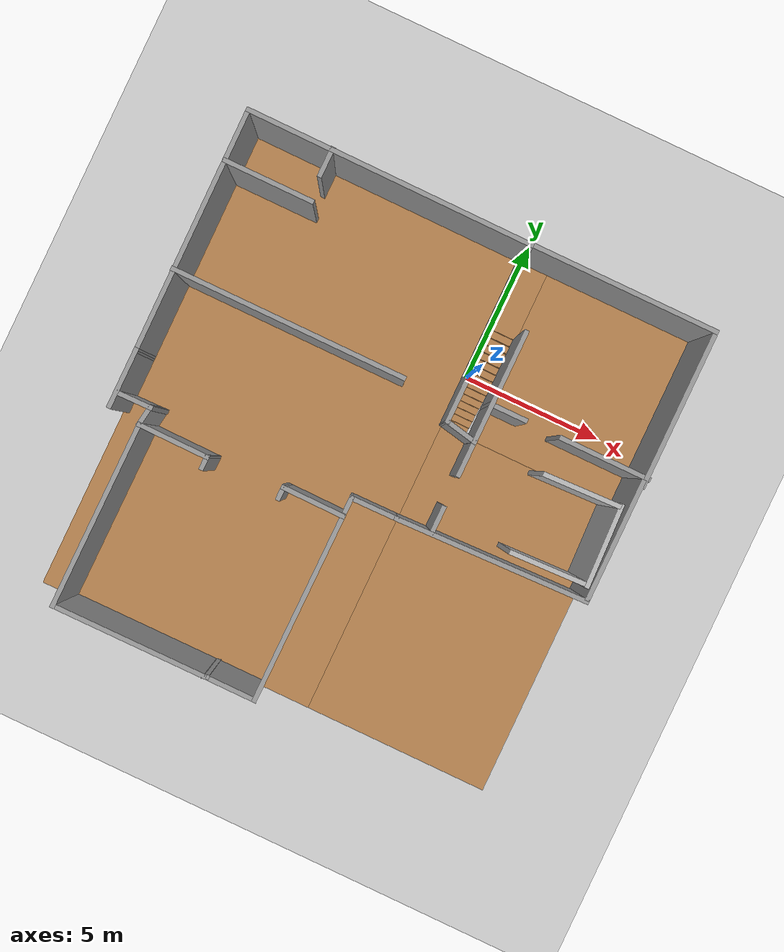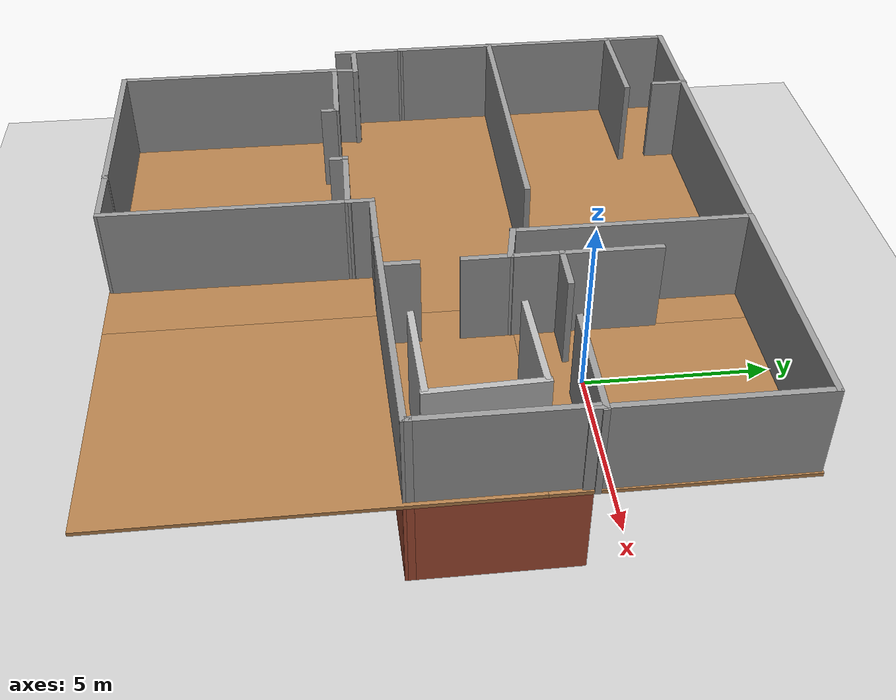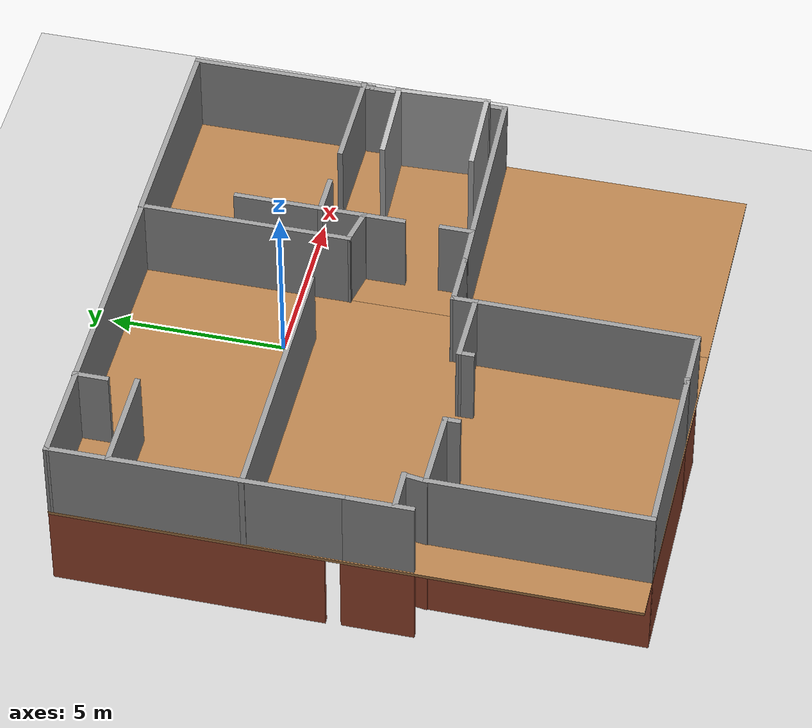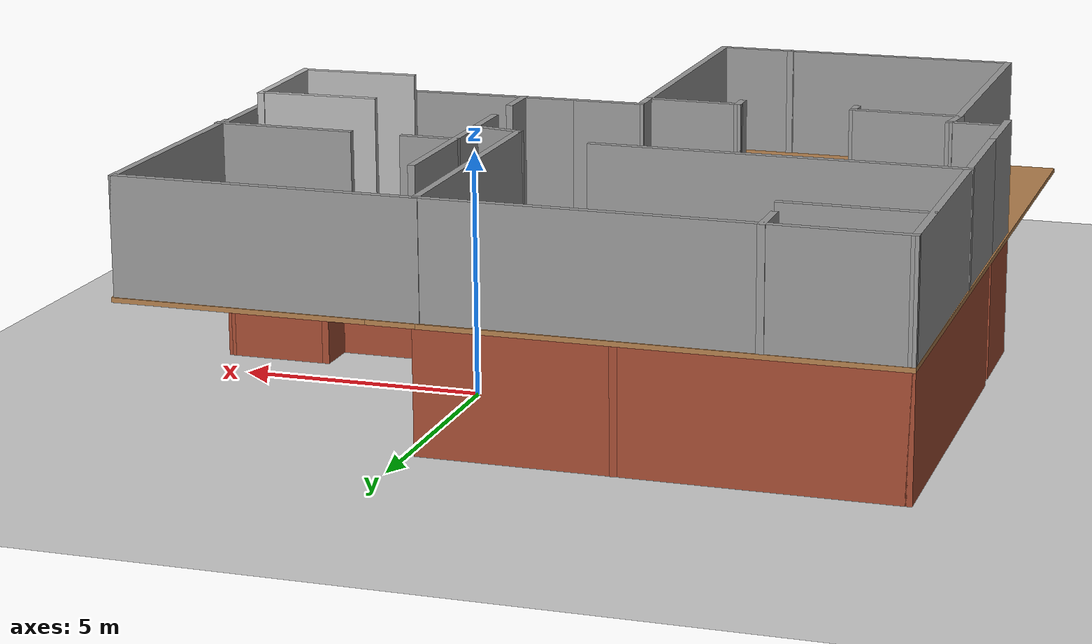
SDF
<sdf version="1.6">
 <world name="default">
  <light name="sun" type="directional">
   <pose>0 0 10 0 -0 0</pose>
   <diffuse>0.8 0.8 0.8 1</diffuse>
   <specular>0.2 0.2 0.2 1</specular>
   <attenuation>
    <range>1000</range>
    <constant>0.9</constant>
    <linear>0.01</linear>
    <quadratic>0.001</quadratic>
   </attenuation>
   <direction>-0.5 0.1 -0.9</direction>
  </light>
  <model name="ground_plane">
   <static>1</static>
   <link name="link">
    <collision name="collision">
     <geometry><plane><normal>0 0 1</normal><size>100 100</size></plane></geometry>
     <surface>
      <contact><collide_bitmask>65535</collide_bitmask></contact>
      <friction><ode><mu>100</mu><mu2>50</mu2></ode></friction>
     </surface>
    </collision>
    <visual name="visual">
     <cast_shadows>0</cast_shadows>
     <geometry><plane><normal>0 0 1</normal><size>100 100</size></plane></geometry>
     <material>
      <script><uri>file://media/materials/scripts/gazebo.material</uri><name>Gazebo/Grey</name></script>
     </material>
    </visual>
   </link>
  </model>
  <gravity>0 0 -9.8</gravity>
  <magnetic_field>6e-06 2.3e-05 -4.2e-05</magnetic_field>
  <atmosphere type="adiabatic"/>
  <physics name="default_physics" default="0" type="ode">
   <max_step_size>0.001</max_step_size>
   <real_time_factor>1</real_time_factor>
   <real_time_update_rate>1000</real_time_update_rate>
  </physics>
  <scene><ambient>0.4 0.4 0.4 1</ambient><background>0.7 0.7 0.7 1</background><shadows>1</shadows></scene>
  <audio><device>default</device></audio>
  <spherical_coordinates>
   <surface_model>EARTH_WGS84</surface_model>
   <latitude_deg>0</latitude_deg>
   <longitude_deg>0</longitude_deg>
   <elevation>0</elevation>
   <heading_deg>0</heading_deg>
  </spherical_coordinates>
  <model name="bush_house_simple">
   <pose>-1.82726 -4.05043 0 0 -0 0</pose>
   <link name="Floor_0">
    <pose>0 -0.001831 2.5 0 -0 0</pose>
    <visual name="Floor_0_Visual_0">
     <pose>-3.10828 0 0.05 0 -0 0</pose>
     <geometry><box><size>9.42798 16.0306 0.1</size></box></geometry>
     <material>
      <script><uri>file://media/materials/scripts/gazebo.material</uri><name>Gazebo/Wood</name></script>
      <ambient>0.760784 0.662745 0.627451 1</ambient>
     </material>
     <meta><layer>1</layer></meta>
    </visual>
    <collision name="Floor_0_Collision_0">
     <geometry><box><size>9.42798 16.0306 0.1</size></box></geometry>
     <pose>-3.10828 0 0.05 0 -0 0</pose>
    </collision>
    <visual name="Floor_0_Visual_1">
     <pose>4.71399 -3.0044 0.05 0 -0 0</pose>
     <geometry><box><size>6.21657 10.0218 0.1</size></box></geometry>
     <material>
      <script><uri>file://media/materials/scripts/gazebo.material</uri><name>Gazebo/Wood</name></script>
      <ambient>0.760784 0.662745 0.627451 1</ambient>
     </material>
     <meta><layer>1</layer></meta>
    </visual>
    <collision name="Floor_0_Collision_1">
     <geometry><box><size>6.21657 10.0218 0.1</size></box></geometry>
     <pose>4.71399 -3.0044 0.05 0 -0 0</pose>
    </collision>
    <visual name="Floor_0_Visual_2">
     <pose>5.21399 5.01089 0.05 0 -0 0</pose>
     <geometry><box><size>5.21657 6.0088 0.1</size></box></geometry>
     <material>
      <script><uri>file://media/materials/scripts/gazebo.material</uri><name>Gazebo/Wood</name></script>
      <ambient>0.760784 0.662745 0.627451 1</ambient>
     </material>
     <meta><layer>1</layer></meta>
    </visual>
    <collision name="Floor_0_Collision_2">
     <geometry><box><size>5.21657 6.0088 0.1</size></box></geometry>
     <pose>5.21399 5.01089 0.05 0 -0 0</pose>
    </collision>
    <visual name="Floor_0_Visual_3">
     <pose>2.1057 6.76089 0.05 0 -0 0</pose>
     <geometry><box><size>1 2.5088 0.1</size></box></geometry>
     <material>
      <script><uri>file://media/materials/scripts/gazebo.material</uri><name>Gazebo/Wood</name></script>
      <ambient>0.760784 0.662745 0.627451 1</ambient>
     </material>
     <meta><layer>1</layer></meta>
    </visual>
    <collision name="Floor_0_Collision_3">
     <geometry><box><size>1 2.5088 0.1</size></box></geometry>
     <pose>2.1057 6.76089 0.05 0 -0 0</pose>
    </collision>
   </link>
   <link name="Stairs_0">
    <visual name="Stairs_0_Visual_0">
     <pose>2.1057 2.12133 0.083333 0 -0 -3.14159</pose>
     <geometry><box><size>1 0.233333 0.166667</size></box></geometry>
     <material>
      <script><uri>file://media/materials/scripts/gazebo.material</uri><name>Gazebo/Wood</name></script>
      <ambient>1 1 1 1</ambient>
     </material>
     <meta><layer>0</layer></meta>
    </visual>
    <collision name="Stairs_0_Collision_0">
     <geometry><box><size>1 0.233333 0.166667</size></box></geometry>
     <pose>2.1057 2.12133 0.083333 0 -0 -3.14159</pose>
    </collision>
    <visual name="Stairs_0_Visual_1">
     <pose>2.1057 2.35466 0.25 0 -0 -3.14159</pose>
     <geometry><box><size>1 0.233333 0.166667</size></box></geometry>
     <material>
      <script><uri>file://media/materials/scripts/gazebo.material</uri><name>Gazebo/Wood</name></script>
      <ambient>1 1 1 1</ambient>
     </material>
     <meta><layer>0</layer></meta>
    </visual>
    <collision name="Stairs_0_Collision_1">
     <geometry><box><size>1 0.233333 0.166667</size></box></geometry>
     <pose>2.1057 2.35466 0.25 0 -0 -3.14159</pose>
    </collision>
    <visual name="Stairs_0_Visual_2">
     <pose>2.1057 2.58799 0.416667 0 -0 -3.14159</pose>
     <geometry><box><size>1 0.233333 0.166667</size></box></geometry>
     <material>
      <script><uri>file://media/materials/scripts/gazebo.material</uri><name>Gazebo/Wood</name></script>
      <ambient>1 1 1 1</ambient>
     </material>
     <meta><layer>0</layer></meta>
    </visual>
    <collision name="Stairs_0_Collision_2">
     <geometry><box><size>1 0.233333 0.166667</size></box></geometry>
     <pose>2.1057 2.58799 0.416667 0 -0 -3.14159</pose>
    </collision>
    <visual name="Stairs_0_Visual_3">
     <pose>2.1057 2.82133 0.583333 0 -0 -3.14159</pose>
     <geometry><box><size>1 0.233333 0.166667</size></box></geometry>
     <material>
      <script><uri>file://media/materials/scripts/gazebo.material</uri><name>Gazebo/Wood</name></script>
      <ambient>1 1 1 1</ambient>
     </material>
     <meta><layer>0</layer></meta>
    </visual>
    <collision name="Stairs_0_Collision_3">
     <geometry><box><size>1 0.233333 0.166667</size></box></geometry>
     <pose>2.1057 2.82133 0.583333 0 -0 -3.14159</pose>
    </collision>
    <visual name="Stairs_0_Visual_4">
     <pose>2.1057 3.05466 0.75 0 -0 -3.14159</pose>
     <geometry><box><size>1 0.233333 0.166667</size></box></geometry>
     <material>
      <script><uri>file://media/materials/scripts/gazebo.material</uri><name>Gazebo/Wood</name></script>
      <ambient>1 1 1 1</ambient>
     </material>
     <meta><layer>0</layer></meta>
    </visual>
    <collision name="Stairs_0_Collision_4">
     <geometry><box><size>1 0.233333 0.166667</size></box></geometry>
     <pose>2.1057 3.05466 0.75 0 -0 -3.14159</pose>
    </collision>
    <visual name="Stairs_0_Visual_5">
     <pose>2.1057 3.28799 0.916667 0 -0 -3.14159</pose>
     <geometry><box><size>1 0.233333 0.166667</size></box></geometry>
     <material>
      <script><uri>file://media/materials/scripts/gazebo.material</uri><name>Gazebo/Wood</name></script>
      <ambient>1 1 1 1</ambient>
     </material>
     <meta><layer>0</layer></meta>
    </visual>
    <collision name="Stairs_0_Collision_5">
     <geometry><box><size>1 0.233333 0.166667</size></box></geometry>
     <pose>2.1057 3.28799 0.916667 0 -0 -3.14159</pose>
    </collision>
    <visual name="Stairs_0_Visual_6">
     <pose>2.1057 3.52133 1.08333 0 -0 -3.14159</pose>
     <geometry><box><size>1 0.233333 0.166667</size></box></geometry>
     <material>
      <script><uri>file://media/materials/scripts/gazebo.material</uri><name>Gazebo/Wood</name></script>
      <ambient>1 1 1 1</ambient>
     </material>
     <meta><layer>0</layer></meta>
    </visual>
    <collision name="Stairs_0_Collision_6">
     <geometry><box><size>1 0.233333 0.166667</size></box></geometry>
     <pose>2.1057 3.52133 1.08333 0 -0 -3.14159</pose>
    </collision>
    <visual name="Stairs_0_Visual_7">
     <pose>2.1057 3.75466 1.25 0 -0 -3.14159</pose>
     <geometry><box><size>1 0.233333 0.166667</size></box></geometry>
     <material>
      <script><uri>file://media/materials/scripts/gazebo.material</uri><name>Gazebo/Wood</name></script>
      <ambient>1 1 1 1</ambient>
     </material>
     <meta><layer>0</layer></meta>
    </visual>
    <collision name="Stairs_0_Collision_7">
     <geometry><box><size>1 0.233333 0.166667</size></box></geometry>
     <pose>2.1057 3.75466 1.25 0 -0 -3.14159</pose>
    </collision>
    <visual name="Stairs_0_Visual_8">
     <pose>2.1057 3.98799 1.41667 0 -0 -3.14159</pose>
     <geometry><box><size>1 0.233333 0.166667</size></box></geometry>
     <material>
      <script><uri>file://media/materials/scripts/gazebo.material</uri><name>Gazebo/Wood</name></script>
      <ambient>1 1 1 1</ambient>
     </material>
     <meta><layer>0</layer></meta>
    </visual>
    <collision name="Stairs_0_Collision_8">
     <geometry><box><size>1 0.233333 0.166667</size></box></geometry>
     <pose>2.1057 3.98799 1.41667 0 -0 -3.14159</pose>
    </collision>
    <visual name="Stairs_0_Visual_9">
     <pose>2.1057 4.22133 1.58333 0 -0 -3.14159</pose>
     <geometry><box><size>1 0.233333 0.166667</size></box></geometry>
     <material>
      <script><uri>file://media/materials/scripts/gazebo.material</uri><name>Gazebo/Wood</name></script>
      <ambient>1 1 1 1</ambient>
     </material>
     <meta><layer>0</layer></meta>
    </visual>
    <collision name="Stairs_0_Collision_9">
     <geometry><box><size>1 0.233333 0.166667</size></box></geometry>
     <pose>2.1057 4.22133 1.58333 0 -0 -3.14159</pose>
    </collision>
    <visual name="Stairs_0_Visual_10">
     <pose>2.1057 4.45466 1.75 0 -0 -3.14159</pose>
     <geometry><box><size>1 0.233333 0.166667</size></box></geometry>
     <material>
      <script><uri>file://media/materials/scripts/gazebo.material</uri><name>Gazebo/Wood</name></script>
      <ambient>1 1 1 1</ambient>
     </material>
     <meta><layer>0</layer></meta>
    </visual>
    <collision name="Stairs_0_Collision_10">
     <geometry><box><size>1 0.233333 0.166667</size></box></geometry>
     <pose>2.1057 4.45466 1.75 0 -0 -3.14159</pose>
    </collision>
    <visual name="Stairs_0_Visual_11">
     <pose>2.1057 4.68799 1.91667 0 -0 -3.14159</pose>
     <geometry><box><size>1 0.233333 0.166667</size></box></geometry>
     <material>
      <script><uri>file://media/materials/scripts/gazebo.material</uri><name>Gazebo/Wood</name></script>
      <ambient>1 1 1 1</ambient>
     </material>
     <meta><layer>0</layer></meta>
    </visual>
    <collision name="Stairs_0_Collision_11">
     <geometry><box><size>1 0.233333 0.166667</size></box></geometry>
     <pose>2.1057 4.68799 1.91667 0 -0 -3.14159</pose>
    </collision>
    <visual name="Stairs_0_Visual_12">
     <pose>2.1057 4.92133 2.08333 0 -0 -3.14159</pose>
     <geometry><box><size>1 0.233333 0.166667</size></box></geometry>
     <material>
      <script><uri>file://media/materials/scripts/gazebo.material</uri><name>Gazebo/Wood</name></script>
      <ambient>1 1 1 1</ambient>
     </material>
     <meta><layer>0</layer></meta>
    </visual>
    <collision name="Stairs_0_Collision_12">
     <geometry><box><size>1 0.233333 0.166667</size></box></geometry>
     <pose>2.1057 4.92133 2.08333 0 -0 -3.14159</pose>
    </collision>
    <visual name="Stairs_0_Visual_13">
     <pose>2.1057 5.15466 2.25 0 -0 -3.14159</pose>
     <geometry><box><size>1 0.233333 0.166667</size></box></geometry>
     <material>
      <script><uri>file://media/materials/scripts/gazebo.material</uri><name>Gazebo/Wood</name></script>
      <ambient>1 1 1 1</ambient>
     </material>
     <meta><layer>0</layer></meta>
    </visual>
    <collision name="Stairs_0_Collision_13">
     <geometry><box><size>1 0.233333 0.166667</size></box></geometry>
     <pose>2.1057 5.15466 2.25 0 -0 -3.14159</pose>
    </collision>
    <visual name="Stairs_0_Visual_14">
     <pose>2.1057 5.38799 2.41667 0 -0 -3.14159</pose>
     <geometry><box><size>1 0.233333 0.166667</size></box></geometry>
     <material>
      <script><uri>file://media/materials/scripts/gazebo.material</uri><name>Gazebo/Wood</name></script>
      <ambient>1 1 1 1</ambient>
     </material>
     <meta><layer>0</layer></meta>
    </visual>
    <collision name="Stairs_0_Collision_14">
     <geometry><box><size>1 0.233333 0.166667</size></box></geometry>
     <pose>2.1057 5.38799 2.41667 0 -0 -3.14159</pose>
    </collision>
   </link>
   <link name="Wall_0">
    <collision name="Wall_0_Collision">
     <geometry><box><size>2 0.15 2.5</size></box></geometry>
     <pose>0 0 1.25 0 -0 0</pose>
    </collision>
    <visual name="Wall_0_Visual">
     <pose>0 0 1.25 0 -0 0</pose>
     <geometry><box><size>2 0.15 2.5</size></box></geometry>
     <material>
      <script><uri>file://media/materials/scripts/gazebo.material</uri><name>Gazebo/Bricks</name></script>
      <ambient>1 1 1 1</ambient>
     </material>
     <meta><layer>0</layer></meta>
    </visual>
    <pose>-7.71193 -0.907072 0 0 -0 -1.5708</pose>
   </link>
   <link name="Wall_100">
    <collision name="Wall_100_Collision">
     <geometry><box><size>1 0.15 2.5</size></box></geometry>
     <pose>0 0 1.25 0 -0 0</pose>
    </collision>
    <visual name="Wall_100_Visual">
     <pose>0 0 1.25 0 -0 0</pose>
     <geometry><box><size>1 0.15 2.5</size></box></geometry>
     <material>
      <script><uri>file://media/materials/scripts/gazebo.material</uri><name>Gazebo/Grey</name></script>
      <ambient>1 1 1 1</ambient>
     </material>
     <meta><layer>1</layer></meta>
    </visual>
    <pose>2.60162 -0.749585 2.5 0 -0 1.5708</pose>
   </link>
   <link name="Wall_102">
    <collision name="Wall_102_Collision">
     <geometry><box><size>1 0.15 2.5</size></box></geometry>
     <pose>0 0 1.25 0 -0 0</pose>
    </collision>
    <visual name="Wall_102_Visual">
     <pose>0 0 1.25 0 -0 0</pose>
     <geometry><box><size>1 0.15 2.5</size></box></geometry>
     <material>
      <script><uri>file://media/materials/scripts/gazebo.material</uri><name>Gazebo/Grey</name></script>
      <ambient>1 1 1 1</ambient>
     </material>
     <meta><layer>1</layer></meta>
    </visual>
    <pose>-4.98099 7.51346 2.5 0 -0 -1.5708</pose>
   </link>
   <link name="Wall_104">
    <collision name="Wall_104_Collision">
     <geometry><box><size>3 0.15 2.5</size></box></geometry>
     <pose>0 0 1.25 0 -0 0</pose>
    </collision>
    <visual name="Wall_104_Visual">
     <pose>0 0 1.25 0 -0 0</pose>
     <geometry><box><size>3 0.15 2.5</size></box></geometry>
     <material>
      <script><uri>file://media/materials/scripts/gazebo.material</uri><name>Gazebo/Grey</name></script>
      <ambient>1 1 1 1</ambient>
     </material>
     <meta><layer>1</layer></meta>
    </visual>
    <pose>-6.30381 6.26889 2.5 0 -0 0</pose>
   </link>
   <link name="Wall_11">
    <collision name="Wall_11_Collision">
     <geometry><box><size>2.12104 0.15 2.5</size></box></geometry>
     <pose>0 0 1.25 0 -0 0</pose>
    </collision>
    <visual name="Wall_11_Visual">
     <pose>0 0 1.25 0 -0 0</pose>
     <geometry><box><size>2.12104 0.15 2.5</size></box></geometry>
     <material>
      <script><uri>file://media/materials/scripts/gazebo.material</uri><name>Gazebo/Bricks</name></script>
      <ambient>1 1 1 1</ambient>
     </material>
     <meta><layer>0</layer></meta>
    </visual>
    <pose>-0.994074 -1.81997 0 0 -0 -0.007673</pose>
   </link>
   <link name="Wall_12">
    <collision name="Wall_12_Collision">
     <geometry><box><size>0.75 0.15 2.5</size></box></geometry>
     <pose>0 0 1.25 0 -0 0</pose>
    </collision>
    <visual name="Wall_12_Visual">
     <pose>0 0 1.25 0 -0 0</pose>
     <geometry><box><size>0.75 0.15 2.5</size></box></geometry>
     <material>
      <script><uri>file://media/materials/scripts/gazebo.material</uri><name>Gazebo/Bricks</name></script>
      <ambient>1 1 1 1</ambient>
     </material>
     <meta><layer>0</layer></meta>
    </visual>
    <pose>-0.008583 -1.52753 0 0 -0 1.5708</pose>
   </link>
   <link name="Wall_13">
    <collision name="Wall_13_Collision">
     <geometry><box><size>1.62909 0.15 2.5</size></box></geometry>
     <pose>0 0 1.25 0 -0 0</pose>
    </collision>
    <visual name="Wall_13_Visual">
     <pose>0 0 1.25 0 -0 0</pose>
     <geometry><box><size>1.62909 0.15 2.5</size></box></geometry>
     <material>
      <script><uri>file://media/materials/scripts/gazebo.material</uri><name>Gazebo/Bricks</name></script>
      <ambient>1 1 1 1</ambient>
     </material>
     <meta><layer>0</layer></meta>
    </visual>
    <pose>0.730926 -1.21997 0 0 -0 0.010225</pose>
   </link>
   <link name="Wall_18">
    <collision name="Wall_18_Collision">
     <geometry><box><size>0.24317 0.15 2.5</size></box></geometry>
     <pose>0 0 1.25 0 -0 0</pose>
    </collision>
    <visual name="Wall_18_Visual">
     <pose>0 0 1.25 0 -0 0</pose>
     <geometry><box><size>0.24317 0.15 2.5</size></box></geometry>
     <material>
      <script><uri>file://media/materials/scripts/gazebo.material</uri><name>Gazebo/Bricks</name></script>
      <ambient>1 1 1 1</ambient>
     </material>
     <meta><layer>0</layer></meta>
    </visual>
    <pose>-1.67458 -7.9092 0 0 -0 0.221775</pose>
   </link>
   <link name="Wall_19">
    <collision name="Wall_19_Collision">
     <geometry><box><size>1.75 0.15 2.5</size></box></geometry>
     <pose>0 0 1.25 0 -0 0</pose>
    </collision>
    <visual name="Wall_19_Visual">
     <pose>0 0 1.25 0 -0 0</pose>
     <geometry><box><size>1.75 0.15 2.5</size></box></geometry>
     <material>
      <script><uri>file://media/materials/scripts/gazebo.material</uri><name>Gazebo/Bricks</name></script>
      <ambient>1 1 1 1</ambient>
     </material>
     <meta><layer>0</layer></meta>
    </visual>
    <pose>-0.844256 -7.91408 0 0 -0 0</pose>
   </link>
   <link name="Wall_20">
    <collision name="Wall_20_Collision">
     <geometry><box><size>6.25178 0.15 2.5</size></box></geometry>
     <pose>0 0 1.25 0 -0 0</pose>
    </collision>
    <visual name="Wall_20_Visual">
     <pose>0 0 1.25 0 -0 0</pose>
     <geometry><box><size>6.25178 0.15 2.5</size></box></geometry>
     <material>
      <script><uri>file://media/materials/scripts/gazebo.material</uri><name>Gazebo/Bricks</name></script>
      <ambient>1 1 1 1</ambient>
     </material>
     <meta><layer>0</layer></meta>
    </visual>
    <pose>-0.02642 -4.86324 0 0 -0 1.56495</pose>
   </link>
   <link name="Wall_22">
    <collision name="Wall_22_Collision">
     <geometry><box><size>6.13704 0.15 2.5</size></box></geometry>
     <pose>0 0 1.25 0 -0 0</pose>
    </collision>
    <visual name="Wall_22_Visual">
     <pose>0 0 1.25 0 -0 0</pose>
     <geometry><box><size>6.13704 0.15 2.5</size></box></geometry>
     <material>
      <script><uri>file://media/materials/scripts/gazebo.material</uri><name>Gazebo/Bricks</name></script>
      <ambient>1 1 1 1</ambient>
     </material>
     <meta><layer>0</layer></meta>
    </visual>
    <pose>-6.68069 -4.94829 0 0 -0 -1.57451</pose>
   </link>
   <link name="Wall_24">
    <collision name="Wall_24_Collision">
     <geometry><box><size>5.10672 0.15 2.5</size></box></geometry>
     <pose>0 0 1.25 0 -0 0</pose>
    </collision>
    <visual name="Wall_24_Visual">
     <pose>0 0 1.25 0 -0 0</pose>
     <geometry><box><size>5.10672 0.15 2.5</size></box></geometry>
     <material>
      <script><uri>file://media/materials/scripts/gazebo.material</uri><name>Gazebo/Bricks</name></script>
      <ambient>1 1 1 1</ambient>
     </material>
     <meta><layer>0</layer></meta>
    </visual>
    <pose>-4.19836 -7.93062 0 0 -0 0.004506</pose>
   </link>
   <link name="Wall_27">
    <collision name="Wall_27_Collision">
     <geometry><box><size>7.5 0.15 2.5</size></box></geometry>
     <pose>0 0 1.25 0 -0 0</pose>
    </collision>
    <visual name="Wall_27_Visual">
     <pose>0 0 1.25 0 -0 0</pose>
     <geometry><box><size>7.5 0.15 2.5</size></box></geometry>
     <material>
      <script><uri>file://media/materials/scripts/gazebo.material</uri><name>Gazebo/Bricks</name></script>
      <ambient>1 1 1 1</ambient>
     </material>
     <meta><layer>0</layer></meta>
    </visual>
    <pose>-7.74694 4.25546 0 0 -0 1.5708</pose>
   </link>
   <link name="Wall_28">
    <collision name="Wall_28_Collision">
     <geometry><box><size>9.5 0.15 2.5</size></box></geometry>
     <pose>0 0 1.25 0 -0 0</pose>
    </collision>
    <visual name="Wall_28_Visual">
     <pose>0 0 1.25 0 -0 0</pose>
     <geometry><box><size>9.5 0.15 2.5</size></box></geometry>
     <material>
      <script><uri>file://media/materials/scripts/gazebo.material</uri><name>Gazebo/Bricks</name></script>
      <ambient>1 1 1 1</ambient>
     </material>
     <meta><layer>0</layer></meta>
    </visual>
    <pose>-3.07194 7.93046 0 0 -0 0</pose>
   </link>
   <link name="Wall_31">
    <collision name="Wall_31_Collision">
     <geometry><box><size>2.5 0.15 2.5</size></box></geometry>
     <pose>0 0 1.25 0 -0 0</pose>
    </collision>
    <visual name="Wall_31_Visual">
     <pose>0 0 1.25 0 -0 0</pose>
     <geometry><box><size>2.5 0.15 2.5</size></box></geometry>
     <material>
      <script><uri>file://media/materials/scripts/gazebo.material</uri><name>Gazebo/Bricks</name></script>
      <ambient>1 1 1 1</ambient>
     </material>
     <meta><layer>0</layer></meta>
    </visual>
    <pose>-6.5464 4.35254 0 0 -0 0</pose>
   </link>
   <link name="Wall_33">
    <collision name="Wall_33_Collision">
     <geometry><box><size>2.25 0.15 2.5</size></box></geometry>
     <pose>0 0 1.25 0 -0 0</pose>
    </collision>
    <visual name="Wall_33_Visual">
     <pose>0 0 1.25 0 -0 0</pose>
     <geometry><box><size>2.25 0.15 2.5</size></box></geometry>
     <material>
      <script><uri>file://media/materials/scripts/gazebo.material</uri><name>Gazebo/Bricks</name></script>
      <ambient>1 1 1 1</ambient>
     </material>
     <meta><layer>0</layer></meta>
    </visual>
    <pose>-3.39004 4.37243 0 0 -0 0</pose>
   </link>
   <link name="Wall_4">
    <collision name="Wall_4_Collision">
     <geometry><box><size>1.19765 0.15 2.5</size></box></geometry>
     <pose>0 0 1.25 0 -0 0</pose>
    </collision>
    <visual name="Wall_4_Visual">
     <pose>0 0 1.25 0 -0 0</pose>
     <geometry><box><size>1.19765 0.15 2.5</size></box></geometry>
     <material>
      <script><uri>file://media/materials/scripts/gazebo.material</uri><name>Gazebo/Bricks</name></script>
      <ambient>1 1 1 1</ambient>
     </material>
     <meta><layer>0</layer></meta>
    </visual>
    <pose>-7.10771 -1.36235 0 0 -0 0.014436</pose>
   </link>
   <link name="Wall_40">
    <collision name="Wall_40_Collision">
     <geometry><box><size>2 0.15 2.5</size></box></geometry>
     <pose>0 0 1.25 0 -0 0</pose>
    </collision>
    <visual name="Wall_40_Visual">
     <pose>0 0 1.25 0 -0 0</pose>
     <geometry><box><size>2 0.15 2.5</size></box></geometry>
     <material>
      <script><uri>file://media/materials/scripts/gazebo.material</uri><name>Gazebo/Bricks</name></script>
      <ambient>1 1 1 1</ambient>
     </material>
     <meta><layer>0</layer></meta>
    </visual>
    <pose>-1.41504 4.37243 0 0 -0 0</pose>
   </link>
   <link name="Wall_42">
    <collision name="Wall_42_Collision">
     <geometry><box><size>2.5 0.15 2.5</size></box></geometry>
     <pose>0 0 1.25 0 -0 0</pose>
    </collision>
    <visual name="Wall_42_Visual">
     <pose>0 0 1.25 0 -0 0</pose>
     <geometry><box><size>2.5 0.15 2.5</size></box></geometry>
     <material>
      <script><uri>file://media/materials/scripts/gazebo.material</uri><name>Gazebo/Bricks</name></script>
      <ambient>1 1 1 1</ambient>
     </material>
     <meta><layer>0</layer></meta>
    </visual>
    <pose>-2.23418 6.76712 0 0 -0 -1.5708</pose>
   </link>
   <link name="Wall_46">
    <collision name="Wall_46_Collision">
     <geometry><box><size>6 0.15 2.5</size></box></geometry>
     <pose>0 0 1.25 0 -0 0</pose>
    </collision>
    <visual name="Wall_46_Visual">
     <pose>0 0 1.25 0 -0 0</pose>
     <geometry><box><size>6 0.15 2.5</size></box></geometry>
     <material>
      <script><uri>file://media/materials/scripts/gazebo.material</uri><name>Gazebo/Bricks</name></script>
      <ambient>1 1 1 1</ambient>
     </material>
     <meta><layer>0</layer></meta>
    </visual>
    <pose>1.60306 5.00546 0 0 -0 -1.5708</pose>
   </link>
   <link name="Wall_48">
    <collision name="Wall_48_Collision">
     <geometry><box><size>3 0.15 2.5</size></box></geometry>
     <pose>0 0 1.25 0 -0 0</pose>
    </collision>
    <visual name="Wall_48_Visual">
     <pose>0 0 1.25 0 -0 0</pose>
     <geometry><box><size>3 0.15 2.5</size></box></geometry>
     <material>
      <script><uri>file://media/materials/scripts/gazebo.material</uri><name>Gazebo/Bricks</name></script>
      <ambient>1 1 1 1</ambient>
     </material>
     <meta><layer>0</layer></meta>
    </visual>
    <pose>4.12806 2.08046 0 0 -0 0</pose>
   </link>
   <link name="Wall_49">
    <collision name="Wall_49_Collision">
     <geometry><box><size>1 0.15 2.5</size></box></geometry>
     <pose>0 0 1.25 0 -0 0</pose>
    </collision>
    <visual name="Wall_49_Visual">
     <pose>0 0 1.25 0 -0 0</pose>
     <geometry><box><size>1 0.15 2.5</size></box></geometry>
     <material>
      <script><uri>file://media/materials/scripts/gazebo.material</uri><name>Gazebo/Bricks</name></script>
      <ambient>1 1 1 1</ambient>
     </material>
     <meta><layer>0</layer></meta>
    </visual>
    <pose>5.55306 2.50546 0 0 -0 1.5708</pose>
   </link>
   <link name="Wall_5">
    <collision name="Wall_5_Collision">
     <geometry><box><size>0.756081 0.15 2.5</size></box></geometry>
     <pose>0 0 1.25 0 -0 0</pose>
    </collision>
    <visual name="Wall_5_Visual">
     <pose>0 0 1.25 0 -0 0</pose>
     <geometry><box><size>0.756081 0.15 2.5</size></box></geometry>
     <material>
      <script><uri>file://media/materials/scripts/gazebo.material</uri><name>Gazebo/Bricks</name></script>
      <ambient>1 1 1 1</ambient>
     </material>
     <meta><layer>0</layer></meta>
    </visual>
    <pose>-6.64188 -1.65479 0 0 -0 -1.71257</pose>
   </link>
   <link name="Wall_51">
    <collision name="Wall_51_Collision">
     <geometry><box><size>2.25 0.15 2.5</size></box></geometry>
     <pose>0 0 1.25 0 -0 0</pose>
    </collision>
    <visual name="Wall_51_Visual">
     <pose>0 0 1.25 0 -0 0</pose>
     <geometry><box><size>2.25 0.15 2.5</size></box></geometry>
     <material>
      <script><uri>file://media/materials/scripts/gazebo.material</uri><name>Gazebo/Bricks</name></script>
      <ambient>1 1 1 1</ambient>
     </material>
     <meta><layer>0</layer></meta>
    </visual>
    <pose>6.60306 2.93046 0 0 -0 0</pose>
   </link>
   <link name="Wall_52">
    <collision name="Wall_52_Collision">
     <geometry><box><size>4 0.15 2.5</size></box></geometry>
     <pose>0 0 1.25 0 -0 0</pose>
    </collision>
    <visual name="Wall_52_Visual">
     <pose>0 0 1.25 0 -0 0</pose>
     <geometry><box><size>4 0.15 2.5</size></box></geometry>
     <material>
      <script><uri>file://media/materials/scripts/gazebo.material</uri><name>Gazebo/Bricks</name></script>
      <ambient>1 1 1 1</ambient>
     </material>
     <meta><layer>0</layer></meta>
    </visual>
    <pose>7.65306 1.00546 0 0 -0 -1.5708</pose>
   </link>
   <link name="Wall_53">
    <collision name="Wall_53_Collision">
     <geometry><box><size>0.25 0.15 2.5</size></box></geometry>
     <pose>0 0 1.25 0 -0 0</pose>
    </collision>
    <visual name="Wall_53_Visual">
     <pose>0 0 1.25 0 -0 0</pose>
     <geometry><box><size>0.25 0.15 2.5</size></box></geometry>
     <material>
      <script><uri>file://media/materials/scripts/gazebo.material</uri><name>Gazebo/Bricks</name></script>
      <ambient>1 1 1 1</ambient>
     </material>
     <meta><layer>0</layer></meta>
    </visual>
    <pose>7.65306 -0.969537 0 0 -0 -1.5708</pose>
   </link>
   <link name="Wall_54">
    <collision name="Wall_54_Collision">
     <geometry><box><size>6.33563 0.15 2.5</size></box></geometry>
     <pose>0 0 1.25 0 -0 0</pose>
    </collision>
    <visual name="Wall_54_Visual">
     <pose>0 0 1.25 0 -0 0</pose>
     <geometry><box><size>6.33563 0.15 2.5</size></box></geometry>
     <material>
      <script><uri>file://media/materials/scripts/gazebo.material</uri><name>Gazebo/Bricks</name></script>
      <ambient>1 1 1 1</ambient>
     </material>
     <meta><layer>0</layer></meta>
    </visual>
    <pose>4.56175 -1.11597 0 0 -0 -3.11041</pose>
   </link>
   <link name="Wall_56">
    <collision name="Wall_56_Collision">
     <geometry><box><size>2 0.15 2.5</size></box></geometry>
     <pose>0 0 1.25 0 -0 0</pose>
    </collision>
    <visual name="Wall_56_Visual">
     <pose>0 0 1.25 0 -0 0</pose>
     <geometry><box><size>2 0.15 2.5</size></box></geometry>
     <material>
      <script><uri>file://media/materials/scripts/gazebo.material</uri><name>Gazebo/Grey</name></script>
      <ambient>1 1 1 1</ambient>
     </material>
     <meta><layer>1</layer></meta>
    </visual>
    <pose>-7.71193 -0.907072 2.5 0 -0 -1.5708</pose>
   </link>
   <link name="Wall_57">
    <collision name="Wall_57_Collision">
     <geometry><box><size>1.19765 0.15 2.5</size></box></geometry>
     <pose>0 0 1.25 0 -0 0</pose>
    </collision>
    <visual name="Wall_57_Visual">
     <pose>0 0 1.25 0 -0 0</pose>
     <geometry><box><size>1.19765 0.15 2.5</size></box></geometry>
     <material>
      <script><uri>file://media/materials/scripts/gazebo.material</uri><name>Gazebo/Grey</name></script>
      <ambient>1 1 1 1</ambient>
     </material>
     <meta><layer>1</layer></meta>
    </visual>
    <pose>-7.10771 -1.36235 2.5 0 -0 0.014436</pose>
   </link>
   <link name="Wall_58">
    <collision name="Wall_58_Collision">
     <geometry><box><size>0.756081 0.15 2.5</size></box></geometry>
     <pose>0 0 1.25 0 -0 0</pose>
    </collision>
    <visual name="Wall_58_Visual">
     <pose>0 0 1.25 0 -0 0</pose>
     <geometry><box><size>0.756081 0.15 2.5</size></box></geometry>
     <material>
      <script><uri>file://media/materials/scripts/gazebo.material</uri><name>Gazebo/Grey</name></script>
      <ambient>1 1 1 1</ambient>
     </material>
     <meta><layer>1</layer></meta>
    </visual>
    <pose>-6.64188 -1.65478 2.5 0 -0 -1.71257</pose>
   </link>
   <link name="Wall_59">
    <collision name="Wall_59_Collision">
     <geometry><box><size>2.38815 0.15 2.5</size></box></geometry>
     <pose>0 0 1.25 0 -0 0</pose>
    </collision>
    <visual name="Wall_59_Visual">
     <pose>0 0 1.25 0 -0 0</pose>
     <geometry><box><size>2.38815 0.15 2.5</size></box></geometry>
     <material>
      <script><uri>file://media/materials/scripts/gazebo.material</uri><name>Gazebo/Grey</name></script>
      <ambient>1 1 1 1</ambient>
     </material>
     <meta><layer>1</layer></meta>
    </visual>
    <pose>-5.55053 -1.96235 2.5 0 -0 -0.006757</pose>
   </link>
   <link name="Wall_6">
    <collision name="Wall_6_Collision">
     <geometry><box><size>2.38815 0.15 2.5</size></box></geometry>
     <pose>0 0 1.25 0 -0 0</pose>
    </collision>
    <visual name="Wall_6_Visual">
     <pose>0 0 1.25 0 -0 0</pose>
     <geometry><box><size>2.38815 0.15 2.5</size></box></geometry>
     <material>
      <script><uri>file://media/materials/scripts/gazebo.material</uri><name>Gazebo/Bricks</name></script>
      <ambient>1 1 1 1</ambient>
     </material>
     <meta><layer>0</layer></meta>
    </visual>
    <pose>-5.55053 -1.96235 0 0 -0 -0.006757</pose>
   </link>
   <link name="Wall_60">
    <collision name="Wall_60_Collision">
     <geometry><box><size>0.5 0.15 2.5</size></box></geometry>
     <pose>0 0 1.25 0 -0 0</pose>
    </collision>
    <visual name="Wall_60_Visual">
     <pose>0 0 1.25 0 -0 0</pose>
     <geometry><box><size>0.5 0.15 2.5</size></box></geometry>
     <material>
      <script><uri>file://media/materials/scripts/gazebo.material</uri><name>Gazebo/Grey</name></script>
      <ambient>1 1 1 1</ambient>
     </material>
     <meta><layer>1</layer></meta>
    </visual>
    <pose>-4.43148 -2.14491 2.5 0 -0 -1.5708</pose>
   </link>
   <link name="Wall_61">
    <collision name="Wall_61_Collision">
     <geometry><box><size>0.5 0.15 2.5</size></box></geometry>
     <pose>0 0 1.25 0 -0 0</pose>
    </collision>
    <visual name="Wall_61_Visual">
     <pose>0 0 1.25 0 -0 0</pose>
     <geometry><box><size>0.5 0.15 2.5</size></box></geometry>
     <material>
      <script><uri>file://media/materials/scripts/gazebo.material</uri><name>Gazebo/Grey</name></script>
      <ambient>1 1 1 1</ambient>
     </material>
     <meta><layer>1</layer></meta>
    </visual>
    <pose>-1.97957 -1.98741 2.5 0 -0 -1.5708</pose>
   </link>
   <link name="Wall_62">
    <collision name="Wall_62_Collision">
     <geometry><box><size>2.12104 0.15 2.5</size></box></geometry>
     <pose>0 0 1.25 0 -0 0</pose>
    </collision>
    <visual name="Wall_62_Visual">
     <pose>0 0 1.25 0 -0 0</pose>
     <geometry><box><size>2.12104 0.15 2.5</size></box></geometry>
     <material>
      <script><uri>file://media/materials/scripts/gazebo.material</uri><name>Gazebo/Grey</name></script>
      <ambient>1 1 1 1</ambient>
     </material>
     <meta><layer>1</layer></meta>
    </visual>
    <pose>-0.994074 -1.81997 2.5 0 -0 -0.007673</pose>
   </link>
   <link name="Wall_63">
    <collision name="Wall_63_Collision">
     <geometry><box><size>0.75 0.15 2.5</size></box></geometry>
     <pose>0 0 1.25 0 -0 0</pose>
    </collision>
    <visual name="Wall_63_Visual">
     <pose>0 0 1.25 0 -0 0</pose>
     <geometry><box><size>0.75 0.15 2.5</size></box></geometry>
     <material>
      <script><uri>file://media/materials/scripts/gazebo.material</uri><name>Gazebo/Grey</name></script>
      <ambient>1 1 1 1</ambient>
     </material>
     <meta><layer>1</layer></meta>
    </visual>
    <pose>-0.008583 -1.52753 2.5 0 -0 1.5708</pose>
   </link>
   <link name="Wall_64">
    <collision name="Wall_64_Collision">
     <geometry><box><size>1.62909 0.15 2.5</size></box></geometry>
     <pose>0 0 1.25 0 -0 0</pose>
    </collision>
    <visual name="Wall_64_Visual">
     <pose>0 0 1.25 0 -0 0</pose>
     <geometry><box><size>1.62909 0.15 2.5</size></box></geometry>
     <material>
      <script><uri>file://media/materials/scripts/gazebo.material</uri><name>Gazebo/Grey</name></script>
      <ambient>1 1 1 1</ambient>
     </material>
     <meta><layer>1</layer></meta>
    </visual>
    <pose>0.730926 -1.21997 2.5 0 -0 0.010225</pose>
   </link>
   <link name="Wall_65">
    <collision name="Wall_65_Collision">
     <geometry><box><size>0.24317 0.15 2.5</size></box></geometry>
     <pose>0 0 1.25 0 -0 0</pose>
    </collision>
    <visual name="Wall_65_Visual">
     <pose>0 0 1.25 0 -0 0</pose>
     <geometry><box><size>0.24317 0.15 2.5</size></box></geometry>
     <material>
      <script><uri>file://media/materials/scripts/gazebo.material</uri><name>Gazebo/Grey</name></script>
      <ambient>1 1 1 1</ambient>
     </material>
     <meta><layer>1</layer></meta>
    </visual>
    <pose>-1.67458 -7.9092 2.5 0 -0 0.221775</pose>
   </link>
   <link name="Wall_66">
    <collision name="Wall_66_Collision">
     <geometry><box><size>1.75 0.15 2.5</size></box></geometry>
     <pose>0 0 1.25 0 -0 0</pose>
    </collision>
    <visual name="Wall_66_Visual">
     <pose>0 0 1.25 0 -0 0</pose>
     <geometry><box><size>1.75 0.15 2.5</size></box></geometry>
     <material>
      <script><uri>file://media/materials/scripts/gazebo.material</uri><name>Gazebo/Grey</name></script>
      <ambient>1 1 1 1</ambient>
     </material>
     <meta><layer>1</layer></meta>
    </visual>
    <pose>-0.844256 -7.91408 2.5 0 -0 0</pose>
   </link>
   <link name="Wall_67">
    <collision name="Wall_67_Collision">
     <geometry><box><size>6.25178 0.15 2.5</size></box></geometry>
     <pose>0 0 1.25 0 -0 0</pose>
    </collision>
    <visual name="Wall_67_Visual">
     <pose>0 0 1.25 0 -0 0</pose>
     <geometry><box><size>6.25178 0.15 2.5</size></box></geometry>
     <material>
      <script><uri>file://media/materials/scripts/gazebo.material</uri><name>Gazebo/Grey</name></script>
      <ambient>1 1 1 1</ambient>
     </material>
     <meta><layer>1</layer></meta>
    </visual>
    <pose>-0.02642 -4.86324 2.5 0 -0 1.56495</pose>
   </link>
   <link name="Wall_68">
    <collision name="Wall_68_Collision">
     <geometry><box><size>6.13704 0.15 2.5</size></box></geometry>
     <pose>0 0 1.25 0 -0 0</pose>
    </collision>
    <visual name="Wall_68_Visual">
     <pose>0 0 1.25 0 -0 0</pose>
     <geometry><box><size>6.13704 0.15 2.5</size></box></geometry>
     <material>
      <script><uri>file://media/materials/scripts/gazebo.material</uri><name>Gazebo/Grey</name></script>
      <ambient>1 1 1 1</ambient>
     </material>
     <meta><layer>1</layer></meta>
    </visual>
    <pose>-6.68069 -4.94829 2.5 0 -0 -1.57451</pose>
   </link>
   <link name="Wall_69">
    <collision name="Wall_69_Collision">
     <geometry><box><size>5.10672 0.15 2.5</size></box></geometry>
     <pose>0 0 1.25 0 -0 0</pose>
    </collision>
    <visual name="Wall_69_Visual">
     <pose>0 0 1.25 0 -0 0</pose>
     <geometry><box><size>5.10672 0.15 2.5</size></box></geometry>
     <material>
      <script><uri>file://media/materials/scripts/gazebo.material</uri><name>Gazebo/Grey</name></script>
      <ambient>1 1 1 1</ambient>
     </material>
     <meta><layer>1</layer></meta>
    </visual>
    <pose>-4.19836 -7.93062 2.5 0 -0 0.004506</pose>
   </link>
   <link name="Wall_7">
    <collision name="Wall_7_Collision">
     <geometry><box><size>0.5 0.15 2.5</size></box></geometry>
     <pose>0 0 1.25 0 -0 0</pose>
    </collision>
    <visual name="Wall_7_Visual">
     <pose>0 0 1.25 0 -0 0</pose>
     <geometry><box><size>0.5 0.15 2.5</size></box></geometry>
     <material>
      <script><uri>file://media/materials/scripts/gazebo.material</uri><name>Gazebo/Bricks</name></script>
      <ambient>1 1 1 1</ambient>
     </material>
     <meta><layer>0</layer></meta>
    </visual>
    <pose>-4.43148 -2.14491 0 0 -0 -1.5708</pose>
   </link>
   <link name="Wall_71">
    <collision name="Wall_71_Collision">
     <geometry><box><size>9.5 0.15 2.5</size></box></geometry>
     <pose>0 0 1.25 0 -0 0</pose>
    </collision>
    <visual name="Wall_71_Visual">
     <pose>0 0 1.25 0 -0 0</pose>
     <geometry><box><size>9.5 0.15 2.5</size></box></geometry>
     <material>
      <script><uri>file://media/materials/scripts/gazebo.material</uri><name>Gazebo/Grey</name></script>
      <ambient>1 1 1 1</ambient>
     </material>
     <meta><layer>1</layer></meta>
    </visual>
    <pose>-3.07194 7.91307 2.5 0 -0 -0.00372</pose>
   </link>
   <link name="Wall_76">
    <collision name="Wall_76_Collision">
     <geometry><box><size>6 0.15 2.5</size></box></geometry>
     <pose>0 0 1.25 0 -0 0</pose>
    </collision>
    <visual name="Wall_76_Visual">
     <pose>0 0 1.25 0 -0 0</pose>
     <geometry><box><size>6 0.15 2.5</size></box></geometry>
     <material>
      <script><uri>file://media/materials/scripts/gazebo.material</uri><name>Gazebo/Grey</name></script>
      <ambient>1 1 1 1</ambient>
     </material>
     <meta><layer>1</layer></meta>
    </visual>
    <pose>1.60306 4.98807 2.5 0 -0 -1.5708</pose>
   </link>
   <link name="Wall_80">
    <collision name="Wall_80_Collision">
     <geometry><box><size>4 0.15 2.5</size></box></geometry>
     <pose>0 0 1.25 0 -0 0</pose>
    </collision>
    <visual name="Wall_80_Visual">
     <pose>0 0 1.25 0 -0 0</pose>
     <geometry><box><size>4 0.15 2.5</size></box></geometry>
     <material>
      <script><uri>file://media/materials/scripts/gazebo.material</uri><name>Gazebo/Grey</name></script>
      <ambient>1 1 1 1</ambient>
     </material>
     <meta><layer>1</layer></meta>
    </visual>
    <pose>7.65306 1.00546 2.5 0 -0 -1.5708</pose>
   </link>
   <link name="Wall_81">
    <collision name="Wall_81_Collision">
     <geometry><box><size>0.25 0.15 2.5</size></box></geometry>
     <pose>0 0 1.25 0 -0 0</pose>
    </collision>
    <visual name="Wall_81_Visual">
     <pose>0 0 1.25 0 -0 0</pose>
     <geometry><box><size>0.25 0.15 2.5</size></box></geometry>
     <material>
      <script><uri>file://media/materials/scripts/gazebo.material</uri><name>Gazebo/Grey</name></script>
      <ambient>1 1 1 1</ambient>
     </material>
     <meta><layer>1</layer></meta>
    </visual>
    <pose>7.65306 -0.969537 2.5 0 -0 -1.5708</pose>
   </link>
   <link name="Wall_82">
    <collision name="Wall_82_Collision">
     <geometry><box><size>6.33563 0.15 2.5</size></box></geometry>
     <pose>0 0 1.25 0 -0 0</pose>
    </collision>
    <visual name="Wall_82_Visual">
     <pose>0 0 1.25 0 -0 0</pose>
     <geometry><box><size>6.33563 0.15 2.5</size></box></geometry>
     <material>
      <script><uri>file://media/materials/scripts/gazebo.material</uri><name>Gazebo/Grey</name></script>
      <ambient>1 1 1 1</ambient>
     </material>
     <meta><layer>1</layer></meta>
    </visual>
    <pose>4.56175 -1.11597 2.5 0 -0 -3.11041</pose>
   </link>
   <link name="Wall_83">
    <collision name="Wall_83_Collision">
     <geometry><box><size>6.25 0.15 2.5</size></box></geometry>
     <pose>0 0 1.25 0 -0 0</pose>
    </collision>
    <visual name="Wall_83_Visual">
     <pose>0 0 1.25 0 -0 0</pose>
     <geometry><box><size>6.25 0.15 2.5</size></box></geometry>
     <material>
      <script><uri>file://media/materials/scripts/gazebo.material</uri><name>Gazebo/Grey</name></script>
      <ambient>1 1 1 1</ambient>
     </material>
     <meta><layer>1</layer></meta>
    </visual>
    <pose>4.65306 7.91307 2.5 0 -0 0</pose>
   </link>
   <link name="Wall_84">
    <collision name="Wall_84_Collision">
     <geometry><box><size>5.25 0.15 2.5</size></box></geometry>
     <pose>0 0 1.25 0 -0 0</pose>
    </collision>
    <visual name="Wall_84_Visual">
     <pose>0 0 1.25 0 -0 0</pose>
     <geometry><box><size>5.25 0.15 2.5</size></box></geometry>
     <material>
      <script><uri>file://media/materials/scripts/gazebo.material</uri><name>Gazebo/Grey</name></script>
      <ambient>1 1 1 1</ambient>
     </material>
     <meta><layer>1</layer></meta>
    </visual>
    <pose>7.70306 5.36307 2.5 0 -0 -1.5708</pose>
   </link>
   <link name="Wall_86">
    <collision name="Wall_86_Collision">
     <geometry><box><size>7.75 0.15 2.5</size></box></geometry>
     <pose>0 0 1.25 0 -0 0</pose>
    </collision>
    <visual name="Wall_86_Visual">
     <pose>0 0 1.25 0 -0 0</pose>
     <geometry><box><size>7.75 0.15 2.5</size></box></geometry>
     <material>
      <script><uri>file://media/materials/scripts/gazebo.material</uri><name>Gazebo/Grey</name></script>
      <ambient>1 1 1 1</ambient>
     </material>
     <meta><layer>1</layer></meta>
    </visual>
    <pose>-3.94214 2.68077 2.5 0 -0 0</pose>
   </link>
   <link name="Wall_88">
    <collision name="Wall_88_Collision">
     <geometry><box><size>8.06261 0.15 2.5</size></box></geometry>
     <pose>0 0 1.25 0 -0 0</pose>
    </collision>
    <visual name="Wall_88_Visual">
     <pose>0 0 1.25 0 -0 0</pose>
     <geometry><box><size>8.06261 0.15 2.5</size></box></geometry>
     <material>
      <script><uri>file://media/materials/scripts/gazebo.material</uri><name>Gazebo/Grey</name></script>
      <ambient>1 1 1 1</ambient>
     </material>
     <meta><layer>1</layer></meta>
    </visual>
    <pose>-7.72944 3.97419 2.5 0 -0 -1.56637</pose>
   </link>
   <link name="Wall_9">
    <collision name="Wall_9_Collision">
     <geometry><box><size>0.5 0.15 2.5</size></box></geometry>
     <pose>0 0 1.25 0 -0 0</pose>
    </collision>
    <visual name="Wall_9_Visual">
     <pose>0 0 1.25 0 -0 0</pose>
     <geometry><box><size>0.5 0.15 2.5</size></box></geometry>
     <material>
      <script><uri>file://media/materials/scripts/gazebo.material</uri><name>Gazebo/Bricks</name></script>
      <ambient>1 1 1 1</ambient>
     </material>
     <meta><layer>0</layer></meta>
    </visual>
    <pose>-1.97957 -1.98741 0 0 -0 -1.5708</pose>
   </link>
   <link name="Wall_90">
    <collision name="Wall_90_Collision">
     <geometry><box><size>3.75 0.15 2.5</size></box></geometry>
     <pose>0 0 1.25 0 -0 0</pose>
    </collision>
    <visual name="Wall_90_Visual">
     <pose>0 0 1.25 0 -0 0</pose>
     <geometry><box><size>3.75 0.15 2.5</size></box></geometry>
     <material>
      <script><uri>file://media/materials/scripts/gazebo.material</uri><name>Gazebo/Grey</name></script>
      <ambient>1 1 1 1</ambient>
     </material>
     <meta><layer>1</layer></meta>
    </visual>
    <pose>2.5883 3.66337 2.5 0 -0 -1.5708</pose>
   </link>
   <link name="Wall_91">
    <collision name="Wall_91_Collision">
     <geometry><box><size>1.15527 0.15 2.5</size></box></geometry>
     <pose>0 0 1.25 0 -0 0</pose>
    </collision>
    <visual name="Wall_91_Visual">
     <pose>0 0 1.25 0 -0 0</pose>
     <geometry><box><size>1.15527 0.15 2.5</size></box></geometry>
     <material>
      <script><uri>file://media/materials/scripts/gazebo.material</uri><name>Gazebo/Grey</name></script>
      <ambient>1 1 1 1</ambient>
     </material>
     <meta><layer>1</layer></meta>
    </visual>
    <pose>2.09568 1.96322 2.5 0 -0 2.94161</pose>
   </link>
   <link name="Wall_94">
    <collision name="Wall_94_Collision">
     <geometry><box><size>1.25 0.15 2.5</size></box></geometry>
     <pose>0 0 1.25 0 -0 0</pose>
    </collision>
    <visual name="Wall_94_Visual">
     <pose>0 0 1.25 0 -0 0</pose>
     <geometry><box><size>1.25 0.15 2.5</size></box></geometry>
     <material>
      <script><uri>file://media/materials/scripts/gazebo.material</uri><name>Gazebo/Grey</name></script>
      <ambient>1 1 1 1</ambient>
     </material>
     <meta><layer>1</layer></meta>
    </visual>
    <pose>3.13423 3.08629 2.5 0 -0 0</pose>
   </link>
   <link name="Wall_96">
    <collision name="Wall_96_Collision">
     <geometry><box><size>3 0.15 2.5</size></box></geometry>
     <pose>0 0 1.25 0 -0 0</pose>
    </collision>
    <visual name="Wall_96_Visual">
     <pose>0 0 1.25 0 -0 0</pose>
     <geometry><box><size>3 0.15 2.5</size></box></geometry>
     <material>
      <script><uri>file://media/materials/scripts/gazebo.material</uri><name>Gazebo/Grey</name></script>
      <ambient>1 1 1 1</ambient>
     </material>
     <meta><layer>1</layer></meta>
    </visual>
    <pose>6.32228 3.06889 2.5 0 -0 0</pose>
   </link>
   <link name="Wall_98">
    <collision name="Wall_98_Collision">
     <geometry><box><size>1.25 0.15 2.5</size></box></geometry>
     <pose>0 0 1.25 0 -0 0</pose>
    </collision>
    <visual name="Wall_98_Visual">
     <pose>0 0 1.25 0 -0 0</pose>
     <geometry><box><size>1.25 0.15 2.5</size></box></geometry>
     <material>
      <script><uri>file://media/materials/scripts/gazebo.material</uri><name>Gazebo/Grey</name></script>
      <ambient>1 1 1 1</ambient>
     </material>
     <meta><layer>1</layer></meta>
    </visual>
    <pose>2.5883 1.31337 2.5 0 -0 -1.5708</pose>
   </link>
   <static>1</static>
  </model>
  <model name="elevator_amzn_0">
   <link name="link">
    <inertial>
     <mass>800</mass>
     <inertia><ixx>1</ixx><ixy>0</ixy><ixz>0</ixz><iyy>1</iyy><iyz>0</iyz><izz>1</izz></inertia>
    </inertial>
    <visual name="floor_visual"><geometry><box><size>2.25 2.25 0.02</size></box></geometry></visual>
    <collision name="floor_collision">
     <geometry><box><size>2.25 2.25 0.02</size></box></geometry>
     <surface>
      <friction>
       <ode><mu>1</mu><mu2>1</mu2><fdir1>0 0 0</fdir1><slip1>0</slip1><slip2>0</slip2></ode>
       <torsional>
        <coefficient>1</coefficient>
        <patch_radius>0</patch_radius>
        <surface_radius>0</surface_radius>
        <use_patch_radius>1</use_patch_radius>
        <ode><slip>0</slip></ode>
       </torsional>
      </friction>
      <bounce><restitution_coefficient>0</restitution_coefficient><threshold>1e+06</threshold></bounce>
      <contact>
       <collide_without_contact>0</collide_without_contact>
       <collide_without_contact_bitmask>1</collide_without_contact_bitmask>
       <collide_bitmask>1</collide_bitmask>
       <ode>
        <soft_cfm>0</soft_cfm>
        <soft_erp>0.2</soft_erp>
        <kp>1e+13</kp>
        <kd>1</kd>
        <max_vel>0.01</max_vel>
        <min_depth>0</min_depth>
       </ode>
       <bullet>
        <split_impulse>1</split_impulse>
        <split_impulse_penetration_threshold>-0.01</split_impulse_penetration_threshold>
        <soft_cfm>0</soft_cfm>
        <soft_erp>0.2</soft_erp>
        <kp>1e+13</kp>
        <kd>1</kd>
       </bullet>
      </contact>
     </surface>
    </collision>
   </link>
   <static>0</static>
   <pose>-7.26532 -9.94569 0.009946 0.000173 -9.8e-05 -0.038592</pose>
  </model>
  <model name="elevator_amzn_2">
   <link name="link">
    <inertial>
     <mass>800</mass>
     <inertia><ixx>1</ixx><ixy>0</ixy><ixz>0</ixz><iyy>1</iyy><iyz>0</iyz><izz>1</izz></inertia>
    </inertial>
    <visual name="floor_visual"><geometry><box><size>2.25 2.25 0.02</size></box></geometry></visual>
    <collision name="floor_collision">
     <geometry><box><size>2.25 2.25 0.02</size></box></geometry>
     <surface>
      <friction>
       <ode><mu>1</mu><mu2>1</mu2><fdir1>0 0 0</fdir1><slip1>0</slip1><slip2>0</slip2></ode>
       <torsional>
        <coefficient>1</coefficient>
        <patch_radius>0</patch_radius>
        <surface_radius>0</surface_radius>
        <use_patch_radius>1</use_patch_radius>
        <ode><slip>0</slip></ode>
       </torsional>
      </friction>
      <bounce><restitution_coefficient>0</restitution_coefficient><threshold>1e+06</threshold></bounce>
      <contact>
       <collide_without_contact>0</collide_without_contact>
       <collide_without_contact_bitmask>1</collide_without_contact_bitmask>
       <collide_bitmask>1</collide_bitmask>
       <ode>
        <soft_cfm>0</soft_cfm>
        <soft_erp>0.2</soft_erp>
        <kp>1e+13</kp>
        <kd>1</kd>
        <max_vel>0.01</max_vel>
        <min_depth>0</min_depth>
       </ode>
       <bullet>
        <split_impulse>1</split_impulse>
        <split_impulse_penetration_threshold>-0.01</split_impulse_penetration_threshold>
        <soft_cfm>0</soft_cfm>
        <soft_erp>0.2</soft_erp>
        <kp>1e+13</kp>
        <kd>1</kd>
       </bullet>
      </contact>
     </surface>
    </collision>
   </link>
   <static>0</static>
   <pose>4.1905 -3.4192 0.009713 -7e-06 -0.000255 0.027649</pose>
  </model>
  <model name="elevator_small_ramp_2">
   <link name="link">
    <inertial>
     <mass>800</mass>
     <inertia><ixx>1</ixx><ixy>0</ixy><ixz>0</ixz><iyy>1</iyy><iyz>0</iyz><izz>1</izz></inertia>
    </inertial>
    <visual name="wall1_visual">
     <pose>1.0745 0.5725 1.125 0 -0 0</pose>
     <geometry><box><size>0.1 1.15 2.25</size></box></geometry>
     <material>
      <script><name>Gazebo/Red</name><uri>__default__</uri></script>
      <shader type="vertex"><normal_map>__default__</normal_map></shader>
      <ambient>1 0 0 1</ambient>
      <diffuse>1 0 0 1</diffuse>
      <specular>0.1 0.1 0.1 1</specular>
      <emissive>0 0 0 1</emissive>
     </material>
    </visual>
    <visual name="wall2_visual">
     <pose>1.0745 -1.0625 1.125 0 -0 0</pose>
     <geometry><box><size>0.1 0.125 2.25</size></box></geometry>
     <material>
      <script><name>Gazebo/Red</name><uri>__default__</uri></script>
      <shader type="vertex"><normal_map>__default__</normal_map></shader>
      <ambient>1 0 0 1</ambient>
      <diffuse>1 0 0 1</diffuse>
      <specular>0.1 0.1 0.1 1</specular>
      <emissive>0 0 0 1</emissive>
     </material>
    </visual>
    <visual name="floor_visual">
     <geometry><box><size>2.25 2.25 0.01</size></box></geometry>
     <material>
      <shader type="vertex"><normal_map>__default__</normal_map></shader>
      <script><name>ModelPreview_1::link::floor_visual_MATERIAL_</name><uri>__default__</uri></script>
      <ambient>0 0 0 1</ambient>
      <diffuse>0 0 0 1</diffuse>
      <specular>0 0 0 1</specular>
      <emissive>0 0 0 1</emissive>
     </material>
    </visual>
    <collision name="wall1_collision">
     <pose>1.0745 0.5725 1.125 0 -0 0</pose>
     <geometry><box><size>0.1 1.15 2.25</size></box></geometry>
     <surface>
      <friction>
       <ode><mu>1</mu><mu2>1</mu2><fdir1>0 0 0</fdir1><slip1>0</slip1><slip2>0</slip2></ode>
       <torsional>
        <coefficient>1</coefficient>
        <patch_radius>0</patch_radius>
        <surface_radius>0</surface_radius>
        <use_patch_radius>1</use_patch_radius>
        <ode><slip>0</slip></ode>
       </torsional>
      </friction>
      <bounce><restitution_coefficient>0</restitution_coefficient><threshold>1e+06</threshold></bounce>
      <contact>
       <collide_without_contact>0</collide_without_contact>
       <collide_without_contact_bitmask>1</collide_without_contact_bitmask>
       <collide_bitmask>1</collide_bitmask>
       <ode>
        <soft_cfm>0</soft_cfm>
        <soft_erp>0.2</soft_erp>
        <kp>1e+13</kp>
        <kd>1</kd>
        <max_vel>0.01</max_vel>
        <min_depth>0</min_depth>
       </ode>
       <bullet>
        <split_impulse>1</split_impulse>
        <split_impulse_penetration_threshold>-0.01</split_impulse_penetration_threshold>
        <soft_cfm>0</soft_cfm>
        <soft_erp>0.2</soft_erp>
        <kp>1e+13</kp>
        <kd>1</kd>
       </bullet>
      </contact>
     </surface>
    </collision>
    <collision name="wall2_collision">
     <pose>1.0745 -1.0625 1.125 0 -0 0</pose>
     <geometry><box><size>0.1 0.125 2.25</size></box></geometry>
     <surface>
      <friction>
       <ode><mu>1</mu><mu2>1</mu2><fdir1>0 0 0</fdir1><slip1>0</slip1><slip2>0</slip2></ode>
       <torsional>
        <coefficient>1</coefficient>
        <patch_radius>0</patch_radius>
        <surface_radius>0</surface_radius>
        <use_patch_radius>1</use_patch_radius>
        <ode><slip>0</slip></ode>
       </torsional>
      </friction>
      <bounce><restitution_coefficient>0</restitution_coefficient><threshold>1e+06</threshold></bounce>
      <contact>
       <collide_without_contact>0</collide_without_contact>
       <collide_without_contact_bitmask>1</collide_without_contact_bitmask>
       <collide_bitmask>1</collide_bitmask>
       <ode>
        <soft_cfm>0</soft_cfm>
        <soft_erp>0.2</soft_erp>
        <kp>1e+13</kp>
        <kd>1</kd>
        <max_vel>0.01</max_vel>
        <min_depth>0</min_depth>
       </ode>
       <bullet>
        <split_impulse>1</split_impulse>
        <split_impulse_penetration_threshold>-0.01</split_impulse_penetration_threshold>
        <soft_cfm>0</soft_cfm>
        <soft_erp>0.2</soft_erp>
        <kp>1e+13</kp>
        <kd>1</kd>
       </bullet>
      </contact>
     </surface>
    </collision>
    <collision name="floor_collision">
     <geometry><box><size>2.25 2.25 0.15</size></box></geometry>
     <surface>
      <friction>
       <ode><mu>1</mu><mu2>1</mu2><fdir1>0 0 0</fdir1><slip1>0</slip1><slip2>0</slip2></ode>
       <torsional>
        <coefficient>1</coefficient>
        <patch_radius>0</patch_radius>
        <surface_radius>0</surface_radius>
        <use_patch_radius>1</use_patch_radius>
        <ode><slip>0</slip></ode>
       </torsional>
      </friction>
      <bounce><restitution_coefficient>0</restitution_coefficient><threshold>1e+06</threshold></bounce>
      <contact>
       <collide_without_contact>0</collide_without_contact>
       <collide_without_contact_bitmask>1</collide_without_contact_bitmask>
       <collide_bitmask>1</collide_bitmask>
       <ode>
        <soft_cfm>0</soft_cfm>
        <soft_erp>0.2</soft_erp>
        <kp>1e+13</kp>
        <kd>1</kd>
        <max_vel>0.01</max_vel>
        <min_depth>0</min_depth>
       </ode>
       <bullet>
        <split_impulse>1</split_impulse>
        <split_impulse_penetration_threshold>-0.01</split_impulse_penetration_threshold>
        <soft_cfm>0</soft_cfm>
        <soft_erp>0.2</soft_erp>
        <kp>1e+13</kp>
        <kd>1</kd>
       </bullet>
      </contact>
     </surface>
    </collision>
   </link>
   <link name="door">
    <pose>1.0745 -0.5 1.125 0 -0 0</pose>
    <inertial>
     <inertia><ixx>1</ixx><ixy>0</ixy><ixz>0</ixz><iyy>1</iyy><iyz>0</iyz><izz>1</izz></inertia>
     <mass>1</mass>
    </inertial>
    <visual name="visual"><geometry><box><size>0.08 1 2.25</size></box></geometry></visual>
    <collision name="collision">
     <geometry><box><size>0.08 1 2.25</size></box></geometry>
     <surface>
      <friction>
       <ode><mu>1</mu><mu2>1</mu2><fdir1>0 0 0</fdir1><slip1>0</slip1><slip2>0</slip2></ode>
       <torsional>
        <coefficient>1</coefficient>
        <patch_radius>0</patch_radius>
        <surface_radius>0</surface_radius>
        <use_patch_radius>1</use_patch_radius>
        <ode><slip>0</slip></ode>
       </torsional>
      </friction>
      <bounce><restitution_coefficient>0</restitution_coefficient><threshold>1e+06</threshold></bounce>
      <contact>
       <collide_without_contact>0</collide_without_contact>
       <collide_without_contact_bitmask>1</collide_without_contact_bitmask>
       <collide_bitmask>1</collide_bitmask>
       <ode>
        <soft_cfm>0</soft_cfm>
        <soft_erp>0.2</soft_erp>
        <kp>1e+13</kp>
        <kd>1</kd>
        <max_vel>0.01</max_vel>
        <min_depth>0</min_depth>
       </ode>
       <bullet>
        <split_impulse>1</split_impulse>
        <split_impulse_penetration_threshold>-0.01</split_impulse_penetration_threshold>
        <soft_cfm>0</soft_cfm>
        <soft_erp>0.2</soft_erp>
        <kp>1e+13</kp>
        <kd>1</kd>
       </bullet>
      </contact>
     </surface>
    </collision>
   </link>
   <joint name="door" type="prismatic">
    <parent>link</parent>
    <child>door</child>
    <axis>
     <xyz>0 1 0</xyz>
     <use_parent_model_frame>0</use_parent_model_frame>
     <limit><lower>0</lower><upper>1</upper><effort>10</effort><velocity>-1</velocity></limit>
     <dynamics>
      <spring_reference>0</spring_reference>
      <spring_stiffness>0</spring_stiffness>
      <damping>2</damping>
      <friction>0</friction>
     </dynamics>
    </axis>
    <physics>
     <ode><limit><cfm>0</cfm><erp>0.2</erp></limit><suspension><cfm>0</cfm><erp>0.2</erp></suspension></ode>
    </physics>
   </joint>
   <static>0</static>
   <plugin name="elevator_plugin" filename="libElevatorPlugin.so">
    <lift_joint>elevator::lift</lift_joint>
    <door_joint>elevator::door</door_joint>
    <floor_height>3.075</floor_height>
    <door_wait_time>10</door_wait_time>
    <topic>~/elevator</topic>
   </plugin>
   <pose>-7.23637 -7.65879 0.074759 0.000288 8.2e-05 -0.03202</pose>
  </model>
  <model name="elevator_small_ramp_2_0">
   <link name="link">
    <inertial>
     <mass>800</mass>
     <inertia><ixx>1</ixx><ixy>0</ixy><ixz>0</ixz><iyy>1</iyy><iyz>0</iyz><izz>1</izz></inertia>
    </inertial>
    <visual name="wall1_visual">
     <pose>1.0745 0.5725 1.125 0 -0 0</pose>
     <geometry><box><size>0.1 1.15 2.25</size></box></geometry>
     <material>
      <script><name>Gazebo/Red</name><uri>__default__</uri></script>
      <shader type="vertex"><normal_map>__default__</normal_map></shader>
      <ambient>1 0 0 1</ambient>
      <diffuse>1 0 0 1</diffuse>
      <specular>0.1 0.1 0.1 1</specular>
      <emissive>0 0 0 1</emissive>
     </material>
    </visual>
    <visual name="wall2_visual">
     <pose>1.0745 -1.0625 1.125 0 -0 0</pose>
     <geometry><box><size>0.1 0.125 2.25</size></box></geometry>
     <material>
      <script><name>Gazebo/Red</name><uri>__default__</uri></script>
      <shader type="vertex"><normal_map>__default__</normal_map></shader>
      <ambient>1 0 0 1</ambient>
      <diffuse>1 0 0 1</diffuse>
      <specular>0.1 0.1 0.1 1</specular>
      <emissive>0 0 0 1</emissive>
     </material>
    </visual>
    <visual name="floor_visual">
     <geometry><box><size>2.25 2.25 0.01</size></box></geometry>
     <material>
      <shader type="vertex"><normal_map>__default__</normal_map></shader>
      <script><name>ModelPreview_1::link::floor_visual_MATERIAL_</name><uri>__default__</uri></script>
      <ambient>0 0 0 1</ambient>
      <diffuse>0 0 0 1</diffuse>
      <specular>0 0 0 1</specular>
      <emissive>0 0 0 1</emissive>
     </material>
    </visual>
    <collision name="wall1_collision">
     <pose>1.0745 0.5725 1.125 0 -0 0</pose>
     <geometry><box><size>0.1 1.15 2.25</size></box></geometry>
     <surface>
      <friction>
       <ode><mu>1</mu><mu2>1</mu2><fdir1>0 0 0</fdir1><slip1>0</slip1><slip2>0</slip2></ode>
       <torsional>
        <coefficient>1</coefficient>
        <patch_radius>0</patch_radius>
        <surface_radius>0</surface_radius>
        <use_patch_radius>1</use_patch_radius>
        <ode><slip>0</slip></ode>
       </torsional>
      </friction>
      <bounce><restitution_coefficient>0</restitution_coefficient><threshold>1e+06</threshold></bounce>
      <contact>
       <collide_without_contact>0</collide_without_contact>
       <collide_without_contact_bitmask>1</collide_without_contact_bitmask>
       <collide_bitmask>1</collide_bitmask>
       <ode>
        <soft_cfm>0</soft_cfm>
        <soft_erp>0.2</soft_erp>
        <kp>1e+13</kp>
        <kd>1</kd>
        <max_vel>0.01</max_vel>
        <min_depth>0</min_depth>
       </ode>
       <bullet>
        <split_impulse>1</split_impulse>
        <split_impulse_penetration_threshold>-0.01</split_impulse_penetration_threshold>
        <soft_cfm>0</soft_cfm>
        <soft_erp>0.2</soft_erp>
        <kp>1e+13</kp>
        <kd>1</kd>
       </bullet>
      </contact>
     </surface>
    </collision>
    <collision name="wall2_collision">
     <pose>1.0745 -1.0625 1.125 0 -0 0</pose>
     <geometry><box><size>0.1 0.125 2.25</size></box></geometry>
     <surface>
      <friction>
       <ode><mu>1</mu><mu2>1</mu2><fdir1>0 0 0</fdir1><slip1>0</slip1><slip2>0</slip2></ode>
       <torsional>
        <coefficient>1</coefficient>
        <patch_radius>0</patch_radius>
        <surface_radius>0</surface_radius>
        <use_patch_radius>1</use_patch_radius>
        <ode><slip>0</slip></ode>
       </torsional>
      </friction>
      <bounce><restitution_coefficient>0</restitution_coefficient><threshold>1e+06</threshold></bounce>
      <contact>
       <collide_without_contact>0</collide_without_contact>
       <collide_without_contact_bitmask>1</collide_without_contact_bitmask>
       <collide_bitmask>1</collide_bitmask>
       <ode>
        <soft_cfm>0</soft_cfm>
        <soft_erp>0.2</soft_erp>
        <kp>1e+13</kp>
        <kd>1</kd>
        <max_vel>0.01</max_vel>
        <min_depth>0</min_depth>
       </ode>
       <bullet>
        <split_impulse>1</split_impulse>
        <split_impulse_penetration_threshold>-0.01</split_impulse_penetration_threshold>
        <soft_cfm>0</soft_cfm>
        <soft_erp>0.2</soft_erp>
        <kp>1e+13</kp>
        <kd>1</kd>
       </bullet>
      </contact>
     </surface>
    </collision>
    <collision name="floor_collision">
     <geometry><box><size>2.25 2.25 0.15</size></box></geometry>
     <surface>
      <friction>
       <ode><mu>1</mu><mu2>1</mu2><fdir1>0 0 0</fdir1><slip1>0</slip1><slip2>0</slip2></ode>
       <torsional>
        <coefficient>1</coefficient>
        <patch_radius>0</patch_radius>
        <surface_radius>0</surface_radius>
        <use_patch_radius>1</use_patch_radius>
        <ode><slip>0</slip></ode>
       </torsional>
      </friction>
      <bounce><restitution_coefficient>0</restitution_coefficient><threshold>1e+06</threshold></bounce>
      <contact>
       <collide_without_contact>0</collide_without_contact>
       <collide_without_contact_bitmask>1</collide_without_contact_bitmask>
       <collide_bitmask>1</collide_bitmask>
       <ode>
        <soft_cfm>0</soft_cfm>
        <soft_erp>0.2</soft_erp>
        <kp>1e+13</kp>
        <kd>1</kd>
        <max_vel>0.01</max_vel>
        <min_depth>0</min_depth>
       </ode>
       <bullet>
        <split_impulse>1</split_impulse>
        <split_impulse_penetration_threshold>-0.01</split_impulse_penetration_threshold>
        <soft_cfm>0</soft_cfm>
        <soft_erp>0.2</soft_erp>
        <kp>1e+13</kp>
        <kd>1</kd>
       </bullet>
      </contact>
     </surface>
    </collision>
   </link>
   <link name="door">
    <pose>1.0745 -0.5 1.125 0 -0 0</pose>
    <inertial>
     <inertia><ixx>1</ixx><ixy>0</ixy><ixz>0</ixz><iyy>1</iyy><iyz>0</iyz><izz>1</izz></inertia>
     <mass>1</mass>
    </inertial>
    <visual name="visual"><geometry><box><size>0.08 1 2.25</size></box></geometry></visual>
    <collision name="collision">
     <geometry><box><size>0.08 1 2.25</size></box></geometry>
     <surface>
      <friction>
       <ode><mu>1</mu><mu2>1</mu2><fdir1>0 0 0</fdir1><slip1>0</slip1><slip2>0</slip2></ode>
       <torsional>
        <coefficient>1</coefficient>
        <patch_radius>0</patch_radius>
        <surface_radius>0</surface_radius>
        <use_patch_radius>1</use_patch_radius>
        <ode><slip>0</slip></ode>
       </torsional>
      </friction>
      <bounce><restitution_coefficient>0</restitution_coefficient><threshold>1e+06</threshold></bounce>
      <contact>
       <collide_without_contact>0</collide_without_contact>
       <collide_without_contact_bitmask>1</collide_without_contact_bitmask>
       <collide_bitmask>1</collide_bitmask>
       <ode>
        <soft_cfm>0</soft_cfm>
        <soft_erp>0.2</soft_erp>
        <kp>1e+13</kp>
        <kd>1</kd>
        <max_vel>0.01</max_vel>
        <min_depth>0</min_depth>
       </ode>
       <bullet>
        <split_impulse>1</split_impulse>
        <split_impulse_penetration_threshold>-0.01</split_impulse_penetration_threshold>
        <soft_cfm>0</soft_cfm>
        <soft_erp>0.2</soft_erp>
        <kp>1e+13</kp>
        <kd>1</kd>
       </bullet>
      </contact>
     </surface>
    </collision>
   </link>
   <joint name="door" type="prismatic">
    <parent>link</parent>
    <child>door</child>
    <axis>
     <xyz>0 1 0</xyz>
     <use_parent_model_frame>0</use_parent_model_frame>
     <limit><lower>0</lower><upper>1</upper><effort>10</effort><velocity>-1</velocity></limit>
     <dynamics>
      <spring_reference>0</spring_reference>
      <spring_stiffness>0</spring_stiffness>
      <damping>2</damping>
      <friction>0</friction>
     </dynamics>
    </axis>
    <physics>
     <ode><limit><cfm>0</cfm><erp>0.2</erp></limit><suspension><cfm>0</cfm><erp>0.2</erp></suspension></ode>
    </physics>
   </joint>
   <static>0</static>
   <plugin name="elevator_plugin" filename="libElevatorPlugin.so">
    <lift_joint>elevator::lift</lift_joint>
    <door_joint>elevator::door</door_joint>
    <floor_height>3.075</floor_height>
    <door_wait_time>10</door_wait_time>
    <topic>~/elevator</topic>
   </plugin>
   <pose>-3.06483 -7.48 0 6e-06 -0.002048 3.13852</pose>
  </model>
  <model name="elevator_shaft">
   <link name="link">
    <visual name="shaft_wall2_visual">
     <pose>0 -1.25 3 0 -0 0</pose>
     <geometry><box><size>2.5 0.15 6</size></box></geometry>
    </visual>
    <visual name="shaft_wall3_visual">
     <pose>-1.25 0 3 0 -0 0</pose>
     <geometry><box><size>0.15 2.7 6</size></box></geometry>
    </visual>
    <visual name="floor0_visual">
     <pose>1.19 0 0.075 0 -0 0</pose>
     <geometry><box><size>0.12 2.5 0.15</size></box></geometry>
    </visual>
    <visual name="floor1_visual">
     <pose>1.19 0 3.075 0 -0 0</pose>
     <geometry><box><size>0.12 2.5 0.15</size></box></geometry>
    </visual>
    <visual name="shaft_wall1_visual">
     <pose>0 1.25 3 0 -0 0</pose>
     <geometry><box><size>2.5 0.15 6</size></box></geometry>
    </visual>
    <collision name="shaft_wall1_collision">
     <pose>0 1.25 3 0 -0 0</pose>
     <geometry><box><size>2.5 0.15 6</size></box></geometry>
     <surface>
      <friction>
       <ode><mu>1</mu><mu2>1</mu2><fdir1>0 0 0</fdir1><slip1>0</slip1><slip2>0</slip2></ode>
       <torsional>
        <coefficient>1</coefficient>
        <patch_radius>0</patch_radius>
        <surface_radius>0</surface_radius>
        <use_patch_radius>1</use_patch_radius>
        <ode><slip>0</slip></ode>
       </torsional>
      </friction>
      <bounce><restitution_coefficient>0</restitution_coefficient><threshold>1e+06</threshold></bounce>
      <contact>
       <collide_without_contact>0</collide_without_contact>
       <collide_without_contact_bitmask>1</collide_without_contact_bitmask>
       <collide_bitmask>1</collide_bitmask>
       <ode>
        <soft_cfm>0</soft_cfm>
        <soft_erp>0.2</soft_erp>
        <kp>1e+13</kp>
        <kd>1</kd>
        <max_vel>0.01</max_vel>
        <min_depth>0</min_depth>
       </ode>
       <bullet>
        <split_impulse>1</split_impulse>
        <split_impulse_penetration_threshold>-0.01</split_impulse_penetration_threshold>
        <soft_cfm>0</soft_cfm>
        <soft_erp>0.2</soft_erp>
        <kp>1e+13</kp>
        <kd>1</kd>
       </bullet>
      </contact>
     </surface>
    </collision>
    <collision name="shaft_wall2_collision">
     <pose>0 -1.25 3 0 -0 0</pose>
     <geometry><box><size>2.5 0.15 6</size></box></geometry>
     <surface>
      <friction>
       <ode><mu>1</mu><mu2>1</mu2><fdir1>0 0 0</fdir1><slip1>0</slip1><slip2>0</slip2></ode>
       <torsional>
        <coefficient>1</coefficient>
        <patch_radius>0</patch_radius>
        <surface_radius>0</surface_radius>
        <use_patch_radius>1</use_patch_radius>
        <ode><slip>0</slip></ode>
       </torsional>
      </friction>
      <bounce><restitution_coefficient>0</restitution_coefficient><threshold>1e+06</threshold></bounce>
      <contact>
       <collide_without_contact>0</collide_without_contact>
       <collide_without_contact_bitmask>1</collide_without_contact_bitmask>
       <collide_bitmask>1</collide_bitmask>
       <ode>
        <soft_cfm>0</soft_cfm>
        <soft_erp>0.2</soft_erp>
        <kp>1e+13</kp>
        <kd>1</kd>
        <max_vel>0.01</max_vel>
        <min_depth>0</min_depth>
       </ode>
       <bullet>
        <split_impulse>1</split_impulse>
        <split_impulse_penetration_threshold>-0.01</split_impulse_penetration_threshold>
        <soft_cfm>0</soft_cfm>
        <soft_erp>0.2</soft_erp>
        <kp>1e+13</kp>
        <kd>1</kd>
       </bullet>
      </contact>
     </surface>
    </collision>
    <collision name="shaft_wall3_collision">
     <pose>-1.25 0 3 0 -0 0</pose>
     <geometry><box><size>0.15 2.7 6</size></box></geometry>
     <surface>
      <friction>
       <ode><mu>1</mu><mu2>1</mu2><fdir1>0 0 0</fdir1><slip1>0</slip1><slip2>0</slip2></ode>
       <torsional>
        <coefficient>1</coefficient>
        <patch_radius>0</patch_radius>
        <surface_radius>0</surface_radius>
        <use_patch_radius>1</use_patch_radius>
        <ode><slip>0</slip></ode>
       </torsional>
      </friction>
      <bounce><restitution_coefficient>0</restitution_coefficient><threshold>1e+06</threshold></bounce>
      <contact>
       <collide_without_contact>0</collide_without_contact>
       <collide_without_contact_bitmask>1</collide_without_contact_bitmask>
       <collide_bitmask>1</collide_bitmask>
       <ode>
        <soft_cfm>0</soft_cfm>
        <soft_erp>0.2</soft_erp>
        <kp>1e+13</kp>
        <kd>1</kd>
        <max_vel>0.01</max_vel>
        <min_depth>0</min_depth>
       </ode>
       <bullet>
        <split_impulse>1</split_impulse>
        <split_impulse_penetration_threshold>-0.01</split_impulse_penetration_threshold>
        <soft_cfm>0</soft_cfm>
        <soft_erp>0.2</soft_erp>
        <kp>1e+13</kp>
        <kd>1</kd>
       </bullet>
      </contact>
     </surface>
    </collision>
    <collision name="floor0_collision">
     <pose>1.19 0 0.075 0 -0 0</pose>
     <geometry><box><size>0.12 2.5 0.15</size></box></geometry>
     <surface>
      <friction>
       <ode><mu>1</mu><mu2>1</mu2><fdir1>0 0 0</fdir1><slip1>0</slip1><slip2>0</slip2></ode>
       <torsional>
        <coefficient>1</coefficient>
        <patch_radius>0</patch_radius>
        <surface_radius>0</surface_radius>
        <use_patch_radius>1</use_patch_radius>
        <ode><slip>0</slip></ode>
       </torsional>
      </friction>
      <bounce><restitution_coefficient>0</restitution_coefficient><threshold>1e+06</threshold></bounce>
      <contact>
       <collide_without_contact>0</collide_without_contact>
       <collide_without_contact_bitmask>1</collide_without_contact_bitmask>
       <collide_bitmask>1</collide_bitmask>
       <ode>
        <soft_cfm>0</soft_cfm>
        <soft_erp>0.2</soft_erp>
        <kp>1e+13</kp>
        <kd>1</kd>
        <max_vel>0.01</max_vel>
        <min_depth>0</min_depth>
       </ode>
       <bullet>
        <split_impulse>1</split_impulse>
        <split_impulse_penetration_threshold>-0.01</split_impulse_penetration_threshold>
        <soft_cfm>0</soft_cfm>
        <soft_erp>0.2</soft_erp>
        <kp>1e+13</kp>
        <kd>1</kd>
       </bullet>
      </contact>
     </surface>
    </collision>
    <collision name="floor1_collision">
     <pose>1.19 0 3.075 0 -0 0</pose>
     <geometry><box><size>0.12 2.5 0.15</size></box></geometry>
     <surface>
      <friction>
       <ode><mu>1</mu><mu2>1</mu2><fdir1>0 0 0</fdir1><slip1>0</slip1><slip2>0</slip2></ode>
       <torsional>
        <coefficient>1</coefficient>
        <patch_radius>0</patch_radius>
        <surface_radius>0</surface_radius>
        <use_patch_radius>1</use_patch_radius>
        <ode><slip>0</slip></ode>
       </torsional>
      </friction>
      <bounce><restitution_coefficient>0</restitution_coefficient><threshold>1e+06</threshold></bounce>
      <contact>
       <collide_without_contact>0</collide_without_contact>
       <collide_without_contact_bitmask>1</collide_without_contact_bitmask>
       <collide_bitmask>1</collide_bitmask>
       <ode>
        <soft_cfm>0</soft_cfm>
        <soft_erp>0.2</soft_erp>
        <kp>1e+13</kp>
        <kd>1</kd>
        <max_vel>0.01</max_vel>
        <min_depth>0</min_depth>
       </ode>
       <bullet>
        <split_impulse>1</split_impulse>
        <split_impulse_penetration_threshold>-0.01</split_impulse_penetration_threshold>
        <soft_cfm>0</soft_cfm>
        <soft_erp>0.2</soft_erp>
        <kp>1e+13</kp>
        <kd>1</kd>
       </bullet>
      </contact>
     </surface>
    </collision>
   </link>
   <static>1</static>
   <pose>4.24493 -3.40542 -0.559123 0 0 -3.10407</pose>
  </model>
  <model name="elevator_small_ramp">
   <link name="link">
    <inertial>
     <mass>800</mass>
     <inertia><ixx>1</ixx><ixy>0</ixy><ixz>0</ixz><iyy>1</iyy><iyz>0</iyz><izz>1</izz></inertia>
    </inertial>
    <visual name="floor_visual">
     <geometry><box><size>2.25 2.25 0.01</size></box></geometry>
     <material>
      <shader type="vertex"><normal_map>__default__</normal_map></shader>
      <script><name>ModelPreview_1::link::floor_visual_MATERIAL_</name><uri>__default__</uri></script>
      <ambient>0 0 0 1</ambient>
      <diffuse>0 0 0 1</diffuse>
      <specular>0 0 0 1</specular>
      <emissive>0 0 0 1</emissive>
     </material>
    </visual>
    <visual name="wall1_visual">
     <pose>1.0745 0.5725 1.125 0 -0 0</pose>
     <geometry><box><size>0.1 1.15 2.25</size></box></geometry>
     <material>
      <script><name>Gazebo/Red</name><uri>__default__</uri></script>
      <shader type="vertex"><normal_map>__default__</normal_map></shader>
      <ambient>1 0 0 1</ambient>
      <diffuse>1 0 0 1</diffuse>
      <specular>0.1 0.1 0.1 1</specular>
      <emissive>0 0 0 1</emissive>
     </material>
    </visual>
    <visual name="wall2_visual">
     <pose>1.0745 -1.0625 1.125 0 -0 0</pose>
     <geometry><box><size>0.1 0.125 2.25</size></box></geometry>
     <material>
      <script><name>Gazebo/Red</name><uri>__default__</uri></script>
      <shader type="vertex"><normal_map>__default__</normal_map></shader>
      <ambient>1 0 0 1</ambient>
      <diffuse>1 0 0 1</diffuse>
      <specular>0.1 0.1 0.1 1</specular>
      <emissive>0 0 0 1</emissive>
     </material>
    </visual>
    <collision name="wall1_collision">
     <pose>1.0745 0.5725 1.125 0 -0 0</pose>
     <geometry><box><size>0.1 1.15 2.25</size></box></geometry>
     <surface>
      <friction>
       <ode><mu>1</mu><mu2>1</mu2><fdir1>0 0 0</fdir1><slip1>0</slip1><slip2>0</slip2></ode>
       <torsional>
        <coefficient>1</coefficient>
        <patch_radius>0</patch_radius>
        <surface_radius>0</surface_radius>
        <use_patch_radius>1</use_patch_radius>
        <ode><slip>0</slip></ode>
       </torsional>
      </friction>
      <bounce><restitution_coefficient>0</restitution_coefficient><threshold>1e+06</threshold></bounce>
      <contact>
       <collide_without_contact>0</collide_without_contact>
       <collide_without_contact_bitmask>1</collide_without_contact_bitmask>
       <collide_bitmask>1</collide_bitmask>
       <ode>
        <soft_cfm>0</soft_cfm>
        <soft_erp>0.2</soft_erp>
        <kp>1e+13</kp>
        <kd>1</kd>
        <max_vel>0.01</max_vel>
        <min_depth>0</min_depth>
       </ode>
       <bullet>
        <split_impulse>1</split_impulse>
        <split_impulse_penetration_threshold>-0.01</split_impulse_penetration_threshold>
        <soft_cfm>0</soft_cfm>
        <soft_erp>0.2</soft_erp>
        <kp>1e+13</kp>
        <kd>1</kd>
       </bullet>
      </contact>
     </surface>
    </collision>
    <collision name="wall2_collision">
     <pose>1.0745 -1.0625 1.125 0 -0 0</pose>
     <geometry><box><size>0.1 0.125 2.25</size></box></geometry>
     <surface>
      <friction>
       <ode><mu>1</mu><mu2>1</mu2><fdir1>0 0 0</fdir1><slip1>0</slip1><slip2>0</slip2></ode>
       <torsional>
        <coefficient>1</coefficient>
        <patch_radius>0</patch_radius>
        <surface_radius>0</surface_radius>
        <use_patch_radius>1</use_patch_radius>
        <ode><slip>0</slip></ode>
       </torsional>
      </friction>
      <bounce><restitution_coefficient>0</restitution_coefficient><threshold>1e+06</threshold></bounce>
      <contact>
       <collide_without_contact>0</collide_without_contact>
       <collide_without_contact_bitmask>1</collide_without_contact_bitmask>
       <collide_bitmask>1</collide_bitmask>
       <ode>
        <soft_cfm>0</soft_cfm>
        <soft_erp>0.2</soft_erp>
        <kp>1e+13</kp>
        <kd>1</kd>
        <max_vel>0.01</max_vel>
        <min_depth>0</min_depth>
       </ode>
       <bullet>
        <split_impulse>1</split_impulse>
        <split_impulse_penetration_threshold>-0.01</split_impulse_penetration_threshold>
        <soft_cfm>0</soft_cfm>
        <soft_erp>0.2</soft_erp>
        <kp>1e+13</kp>
        <kd>1</kd>
       </bullet>
      </contact>
     </surface>
    </collision>
    <collision name="floor_collision">
     <geometry><box><size>2.25 2.25 0.15</size></box></geometry>
     <surface>
      <friction>
       <ode><mu>1</mu><mu2>1</mu2><fdir1>0 0 0</fdir1><slip1>0</slip1><slip2>0</slip2></ode>
       <torsional>
        <coefficient>1</coefficient>
        <patch_radius>0</patch_radius>
        <surface_radius>0</surface_radius>
        <use_patch_radius>1</use_patch_radius>
        <ode><slip>0</slip></ode>
       </torsional>
      </friction>
      <bounce><restitution_coefficient>0</restitution_coefficient><threshold>1e+06</threshold></bounce>
      <contact>
       <collide_without_contact>0</collide_without_contact>
       <collide_without_contact_bitmask>1</collide_without_contact_bitmask>
       <collide_bitmask>1</collide_bitmask>
       <ode>
        <soft_cfm>0</soft_cfm>
        <soft_erp>0.2</soft_erp>
        <kp>1e+13</kp>
        <kd>1</kd>
        <max_vel>0.01</max_vel>
        <min_depth>0</min_depth>
       </ode>
       <bullet>
        <split_impulse>1</split_impulse>
        <split_impulse_penetration_threshold>-0.01</split_impulse_penetration_threshold>
        <soft_cfm>0</soft_cfm>
        <soft_erp>0.2</soft_erp>
        <kp>1e+13</kp>
        <kd>1</kd>
       </bullet>
      </contact>
     </surface>
    </collision>
   </link>
   <link name="door">
    <pose>1.0745 -0.5 1.125 0 -0 0</pose>
    <inertial>
     <inertia><ixx>1</ixx><ixy>0</ixy><ixz>0</ixz><iyy>1</iyy><iyz>0</iyz><izz>1</izz></inertia>
     <mass>1</mass>
    </inertial>
    <visual name="visual"><geometry><box><size>0.08 1 2.25</size></box></geometry></visual>
    <collision name="collision">
     <geometry><box><size>0.08 1 2.25</size></box></geometry>
     <surface>
      <friction>
       <ode><mu>1</mu><mu2>1</mu2><fdir1>0 0 0</fdir1><slip1>0</slip1><slip2>0</slip2></ode>
       <torsional>
        <coefficient>1</coefficient>
        <patch_radius>0</patch_radius>
        <surface_radius>0</surface_radius>
        <use_patch_radius>1</use_patch_radius>
        <ode><slip>0</slip></ode>
       </torsional>
      </friction>
      <bounce><restitution_coefficient>0</restitution_coefficient><threshold>1e+06</threshold></bounce>
      <contact>
       <collide_without_contact>0</collide_without_contact>
       <collide_without_contact_bitmask>1</collide_without_contact_bitmask>
       <collide_bitmask>1</collide_bitmask>
       <ode>
        <soft_cfm>0</soft_cfm>
        <soft_erp>0.2</soft_erp>
        <kp>1e+13</kp>
        <kd>1</kd>
        <max_vel>0.01</max_vel>
        <min_depth>0</min_depth>
       </ode>
       <bullet>
        <split_impulse>1</split_impulse>
        <split_impulse_penetration_threshold>-0.01</split_impulse_penetration_threshold>
        <soft_cfm>0</soft_cfm>
        <soft_erp>0.2</soft_erp>
        <kp>1e+13</kp>
        <kd>1</kd>
       </bullet>
      </contact>
     </surface>
    </collision>
   </link>
   <joint name="door" type="prismatic">
    <parent>link</parent>
    <child>door</child>
    <axis>
     <xyz>0 1 0</xyz>
     <use_parent_model_frame>0</use_parent_model_frame>
     <limit><lower>0</lower><upper>1</upper><effort>10</effort><velocity>-1</velocity></limit>
     <dynamics>
      <spring_reference>0</spring_reference>
      <spring_stiffness>0</spring_stiffness>
      <damping>2</damping>
      <friction>0</friction>
     </dynamics>
    </axis>
    <physics>
     <ode><limit><cfm>0</cfm><erp>0.2</erp></limit><suspension><cfm>0</cfm><erp>0.2</erp></suspension></ode>
    </physics>
   </joint>
   <static>0</static>
   <plugin name="elevator_plugin" filename="libElevatorPlugin.so">
    <lift_joint>elevator::lift</lift_joint>
    <door_joint>elevator::door</door_joint>
    <floor_height>3.075</floor_height>
    <door_wait_time>10</door_wait_time>
    <topic>~/elevator</topic>
   </plugin>
   <pose>-3.06258 -9.97265 0 -8e-05 -0.004198 -3.12253</pose>
  </model>
 </world>
</sdf>
